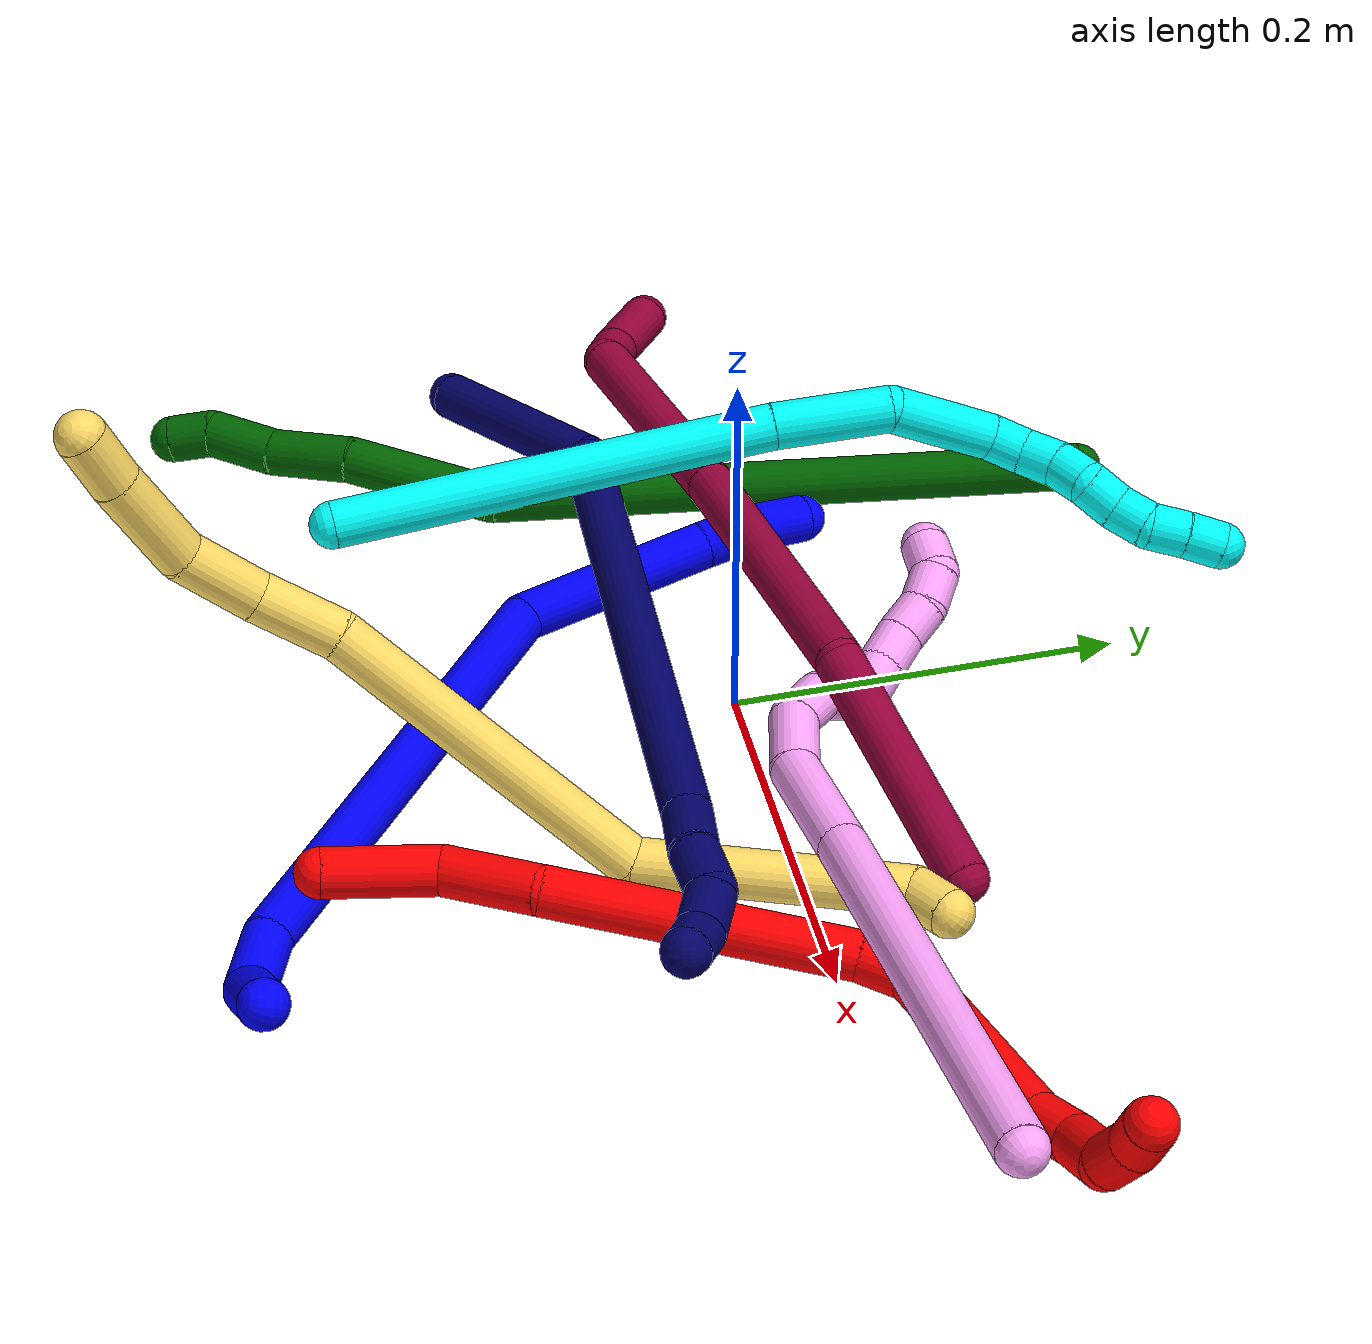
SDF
<sdf version="1.7">
 <world name="default">
  <plugin name="TubeGeneratorPlugin" filename="libtube_generator_plugin.so"/>
  <model name="photoneo_s_sensor">
   <static>1</static>
   <pose>0 0 2 1.57079 1.57079 3.14159</pose>
   <link name="link">
    <inertial><mass>0.1</mass></inertial>
    <sensor name="sensor" type="depth">
     <update_rate>30</update_rate>
     <camera>
      <horizontal_fov>1.22</horizontal_fov>
      <image><width>1920</width><height>1200</height><format>B8G8R8</format></image>
      <clip><near>0.1</near><far>4</far></clip>
      <depth_camera><output>points</output></depth_camera>
     </camera>
     <plugin name="camera_plugin" filename="libgazebo_ros_depth_camera.so">
      <baseline>0.2</baseline>
      <alwaysOn>1</alwaysOn>
      <updateRate>0.0</updateRate>
      <cameraName>camera_ir</cameraName>
      <imageTopicName>/camera/color/image_raw</imageTopicName>
      <cameraInfoTopicName>/camera/color/camera_info</cameraInfoTopicName>
      <depthImageTopicName>/camera/depth/image_raw</depthImageTopicName>
      <depthImageCameraInfoTopicName>/camera/depth/camera_info</depthImageCameraInfoTopicName>
      <pointCloudTopicName>/camera/depth/points</pointCloudTopicName>
      <frameName>fr_optical</frameName>
      <pointCloudCutoff>0.1</pointCloudCutoff>
      <pointCloudCutoffMax>2.0</pointCloudCutoffMax>
      <distortionK1>0</distortionK1>
      <distortionK2>0</distortionK2>
      <distortionK3>0</distortionK3>
      <distortionT1>0</distortionT1>
      <distortionT2>0</distortionT2>
      <CxPrime>0</CxPrime>
      <Cx>0</Cx>
      <Cy>0</Cy>
      <focalLength>0</focalLength>
      <hackBaseline>0</hackBaseline>
     </plugin>
    </sensor>
   </link>
  </model>
  <gravity>0 0 -9.8</gravity>
  <magnetic_field>6e-06 2.3e-05 -4.2e-05</magnetic_field>
  <atmosphere type="adiabatic"/>
  <physics name="default_physics" default="0" type="ode">
   <max_step_size>0.003</max_step_size>
   <real_time_factor>1</real_time_factor>
   <real_time_update_rate>1000</real_time_update_rate>
   <max_contacts>10000</max_contacts>
   <ode>
    <solver>
     <type>quick</type>
     <iters>100</iters>
     <sor>1.3</sor>
     <use_dynamic_moi_rescaling>0</use_dynamic_moi_rescaling>
    </solver>
    <constraints>
     <contact_max_correcting_vel>0</contact_max_correcting_vel>
     <contact_surface_layer>0.001</contact_surface_layer>
     <cfm>0</cfm>
     <erp>0.2</erp>
    </constraints>
   </ode>
  </physics>
  <scene><ambient>0.4 0.4 0.4 1</ambient><background>0.7 0.7 0.7 1</background><shadows>0</shadows></scene>
  <audio><device>default</device></audio>
  <spherical_coordinates>
   <surface_model>EARTH_WGS84</surface_model>
   <latitude_deg>0</latitude_deg>
   <longitude_deg>0</longitude_deg>
   <elevation>0</elevation>
   <heading_deg>0</heading_deg>
  </spherical_coordinates>
  <model name="bin">
   <static>1</static>
   <link name="bottom">
    <collision name="collision-bottom">
     <pose>0 0 -0.01 0 -0 0</pose>
     <geometry><box><size>0.8 0.6 0.02</size></box></geometry>
     <surface>
      <friction><ode><mu>100</mu><mu2>100</mu2></ode></friction>
      <contact><collide_bitmask>65535</collide_bitmask></contact>
     </surface>
    </collision>
   </link>
   <link name="west_wall">
    <collision name="collision-west_wall">
     <pose>-0.41 0 0.1 0 -0 0</pose>
     <geometry><box><size>0.02 0.6 0.2</size></box></geometry>
     <surface>
      <friction><ode><mu>100</mu><mu2>100</mu2></ode></friction>
      <contact><collide_bitmask>65535</collide_bitmask></contact>
     </surface>
    </collision>
   </link>
   <link name="east_wall">
    <collision name="collision-east_wall">
     <pose>0.41 0 0.1 0 -0 0</pose>
     <geometry><box><size>0.02 0.6 0.2</size></box></geometry>
     <surface>
      <friction><ode><mu>100</mu><mu2>100</mu2></ode></friction>
      <contact><collide_bitmask>65535</collide_bitmask></contact>
     </surface>
    </collision>
   </link>
   <link name="south_wall">
    <collision name="collision-south_wall">
     <pose>0 -0.31 0.1 0 -0 0</pose>
     <geometry><box><size>0.8 0.02 0.2</size></box></geometry>
     <surface>
      <friction><ode><mu>100</mu><mu2>100</mu2></ode></friction>
      <contact><collide_bitmask>65535</collide_bitmask></contact>
     </surface>
    </collision>
   </link>
   <link name="north_wall">
    <collision name="collision-north_wall">
     <pose>0 0.31 0.1 0 -0 0</pose>
     <geometry><box><size>0.8 0.02 0.2</size></box></geometry>
     <surface>
      <friction><ode><mu>100</mu><mu2>100</mu2></ode></friction>
      <contact><collide_bitmask>65535</collide_bitmask></contact>
     </surface>
    </collision>
   </link>
  </model>
  <model name="1">
   <static>0</static>
   <link name="1">
    <collision name="collision-cylinder-e_1_1_4">
     <pose>-0.018962 -0.005473 -0.005188 2.32944 -1.19227 -2.01189</pose>
     <geometry><cylinder><radius>0.0125</radius><length>0.040814</length></cylinder></geometry>
     <surface>
      <friction><ode><mu>1.16</mu><mu2>1.16</mu2><slip1>0</slip1><slip2>0</slip2></ode></friction>
      <contact><ode><kp>1e+06</kp><kd>1</kd><max_vel>0</max_vel><min_depth>0.001</min_depth></ode></contact>
     </surface>
    </collision>
    <visual name="visual-cylinder-e_1_1_4">
     <pose>-0.018962 -0.005473 -0.005188 2.32944 -1.19227 -2.01189</pose>
     <geometry><cylinder><radius>0.0125</radius><length>0.040814</length></cylinder></geometry>
     <material><ambient>0 0 1 1</ambient></material>
    </visual>
    <collision name="collision-cylinder-e_2_4_5">
     <pose>-0.052261 -0.00319 -0.017842 -2.33709 -0.926681 1.7308</pose>
     <geometry><cylinder><radius>0.0125</radius><length>0.035857</length></cylinder></geometry>
     <surface>
      <friction><ode><mu>1.16</mu><mu2>1.16</mu2><slip1>0</slip1><slip2>0</slip2></ode></friction>
      <contact><ode><kp>1e+06</kp><kd>1</kd><max_vel>0</max_vel><min_depth>0.001</min_depth></ode></contact>
     </surface>
    </collision>
    <visual name="visual-cylinder-e_2_4_5">
     <pose>-0.052261 -0.00319 -0.017842 -2.33709 -0.926681 1.7308</pose>
     <geometry><cylinder><radius>0.0125</radius><length>0.035857</length></cylinder></geometry>
     <material><ambient>0 0 1 1</ambient></material>
    </visual>
    <collision name="collision-cylinder-e_3_5_6">
     <pose>-0.14315 0.068947 -0.10562 -2.46586 -0.63947 1.51148</pose>
     <geometry><cylinder><radius>0.0125</radius><length>0.256555</length></cylinder></geometry>
     <surface>
      <friction><ode><mu>1.16</mu><mu2>1.16</mu2><slip1>0</slip1><slip2>0</slip2></ode></friction>
      <contact><ode><kp>1e+06</kp><kd>1</kd><max_vel>0</max_vel><min_depth>0.001</min_depth></ode></contact>
     </surface>
    </collision>
    <visual name="visual-cylinder-e_3_5_6">
     <pose>-0.14315 0.068947 -0.10562 -2.46586 -0.63947 1.51148</pose>
     <geometry><cylinder><radius>0.0125</radius><length>0.256555</length></cylinder></geometry>
     <material><ambient>0 0 1 1</ambient></material>
    </visual>
    <collision name="collision-cylinder-e_4_6_7">
     <pose>-0.224131 0.160175 -0.232559 -2.61917 -0.082138 0.305051</pose>
     <geometry><cylinder><radius>0.0125</radius><length>0.107972</length></cylinder></geometry>
     <surface>
      <friction><ode><mu>1.16</mu><mu2>1.16</mu2><slip1>0</slip1><slip2>0</slip2></ode></friction>
      <contact><ode><kp>1e+06</kp><kd>1</kd><max_vel>0</max_vel><min_depth>0.001</min_depth></ode></contact>
     </surface>
    </collision>
    <visual name="visual-cylinder-e_4_6_7">
     <pose>-0.224131 0.160175 -0.232559 -2.61917 -0.082138 0.305051</pose>
     <geometry><cylinder><radius>0.0125</radius><length>0.107972</length></cylinder></geometry>
     <material><ambient>0 0 1 1</ambient></material>
    </visual>
    <collision name="collision-cylinder-e_5_7_8">
     <pose>-0.227278 0.19406 -0.289602 -2.54738 0.101649 -0.32928</pose>
     <geometry><cylinder><radius>0.0125</radius><length>0.025273</length></cylinder></geometry>
     <surface>
      <friction><ode><mu>1.16</mu><mu2>1.16</mu2><slip1>0</slip1><slip2>0</slip2></ode></friction>
      <contact><ode><kp>1e+06</kp><kd>1</kd><max_vel>0</max_vel><min_depth>0.001</min_depth></ode></contact>
     </surface>
    </collision>
    <visual name="visual-cylinder-e_5_7_8">
     <pose>-0.227278 0.19406 -0.289602 -2.54738 0.101649 -0.32928</pose>
     <geometry><cylinder><radius>0.0125</radius><length>0.025273</length></cylinder></geometry>
     <material><ambient>0 0 1 1</ambient></material>
    </visual>
    <collision name="collision-cylinder-e_6_8_2">
     <pose>-0.227291 0.206618 -0.315796 -2.80505 -0.077322 0.44775</pose>
     <geometry><cylinder><radius>0.0125</radius><length>0.033529</length></cylinder></geometry>
     <surface>
      <friction><ode><mu>1.16</mu><mu2>1.16</mu2><slip1>0</slip1><slip2>0</slip2></ode></friction>
      <contact><ode><kp>1e+06</kp><kd>1</kd><max_vel>0</max_vel><min_depth>0.001</min_depth></ode></contact>
     </surface>
    </collision>
    <visual name="visual-cylinder-e_6_8_2">
     <pose>-0.227291 0.206618 -0.315796 -2.80505 -0.077322 0.44775</pose>
     <geometry><cylinder><radius>0.0125</radius><length>0.033529</length></cylinder></geometry>
     <material><ambient>0 0 1 1</ambient></material>
    </visual>
    <collision name="collision-sphere-2">
     <pose>-0.228586 0.212138 -0.331573 0 -0 0</pose>
     <geometry><sphere><radius>0.0125</radius></sphere></geometry>
     <surface>
      <friction><ode><mu>1.16</mu><mu2>1.16</mu2><slip1>0</slip1><slip2>0</slip2></ode></friction>
      <contact><ode><kp>1e+06</kp><kd>1</kd><max_vel>0</max_vel><min_depth>0.001</min_depth></ode></contact>
     </surface>
    </collision>
    <visual name="visual-sphere-2">
     <pose>-0.228586 0.212138 -0.331573 0 -0 0</pose>
     <geometry><sphere><radius>0.0125</radius></sphere></geometry>
     <material><ambient>0 0 1 1</ambient></material>
    </visual>
    <collision name="collision-sphere-4">
     <pose>-0.037925 -0.010947 -0.010376 0 -0 0</pose>
     <geometry><sphere><radius>0.0125</radius></sphere></geometry>
     <surface>
      <friction><ode><mu>1.16</mu><mu2>1.16</mu2><slip1>0</slip1><slip2>0</slip2></ode></friction>
      <contact><ode><kp>1e+06</kp><kd>1</kd><max_vel>0</max_vel><min_depth>0.001</min_depth></ode></contact>
     </surface>
    </collision>
    <visual name="visual-sphere-4">
     <pose>-0.037925 -0.010947 -0.010376 0 -0 0</pose>
     <geometry><sphere><radius>0.0125</radius></sphere></geometry>
     <material><ambient>0 0 1 1</ambient></material>
    </visual>
    <collision name="collision-sphere-1">
     <geometry><sphere><radius>0.0125</radius></sphere></geometry>
     <surface>
      <friction><ode><mu>1.16</mu><mu2>1.16</mu2><slip1>0</slip1><slip2>0</slip2></ode></friction>
      <contact><ode><kp>1e+06</kp><kd>1</kd><max_vel>0</max_vel><min_depth>0.001</min_depth></ode></contact>
     </surface>
    </collision>
    <visual name="visual-sphere-1">
     <geometry><sphere><radius>0.0125</radius></sphere></geometry>
     <material><ambient>0 0 1 1</ambient></material>
    </visual>
    <collision name="collision-sphere-8">
     <pose>-0.225996 0.201098 -0.300019 0 -0 0</pose>
     <geometry><sphere><radius>0.0125</radius></sphere></geometry>
     <surface>
      <friction><ode><mu>1.16</mu><mu2>1.16</mu2><slip1>0</slip1><slip2>0</slip2></ode></friction>
      <contact><ode><kp>1e+06</kp><kd>1</kd><max_vel>0</max_vel><min_depth>0.001</min_depth></ode></contact>
     </surface>
    </collision>
    <visual name="visual-sphere-8">
     <pose>-0.225996 0.201098 -0.300019 0 -0 0</pose>
     <geometry><sphere><radius>0.0125</radius></sphere></geometry>
     <material><ambient>0 0 1 1</ambient></material>
    </visual>
    <collision name="collision-sphere-5">
     <pose>-0.066597 0.004567 -0.025308 0 -0 0</pose>
     <geometry><sphere><radius>0.0125</radius></sphere></geometry>
     <surface>
      <friction><ode><mu>1.16</mu><mu2>1.16</mu2><slip1>0</slip1><slip2>0</slip2></ode></friction>
      <contact><ode><kp>1e+06</kp><kd>1</kd><max_vel>0</max_vel><min_depth>0.001</min_depth></ode></contact>
     </surface>
    </collision>
    <visual name="visual-sphere-5">
     <pose>-0.066597 0.004567 -0.025308 0 -0 0</pose>
     <geometry><sphere><radius>0.0125</radius></sphere></geometry>
     <material><ambient>0 0 1 1</ambient></material>
    </visual>
    <collision name="collision-sphere-6">
     <pose>-0.219702 0.133328 -0.185932 0 -0 0</pose>
     <geometry><sphere><radius>0.0125</radius></sphere></geometry>
     <surface>
      <friction><ode><mu>1.16</mu><mu2>1.16</mu2><slip1>0</slip1><slip2>0</slip2></ode></friction>
      <contact><ode><kp>1e+06</kp><kd>1</kd><max_vel>0</max_vel><min_depth>0.001</min_depth></ode></contact>
     </surface>
    </collision>
    <visual name="visual-sphere-6">
     <pose>-0.219702 0.133328 -0.185932 0 -0 0</pose>
     <geometry><sphere><radius>0.0125</radius></sphere></geometry>
     <material><ambient>0 0 1 1</ambient></material>
    </visual>
    <collision name="collision-sphere-7">
     <pose>-0.22856 0.187022 -0.279186 0 -0 0</pose>
     <geometry><sphere><radius>0.0125</radius></sphere></geometry>
     <surface>
      <friction><ode><mu>1.16</mu><mu2>1.16</mu2><slip1>0</slip1><slip2>0</slip2></ode></friction>
      <contact><ode><kp>1e+06</kp><kd>1</kd><max_vel>0</max_vel><min_depth>0.001</min_depth></ode></contact>
     </surface>
    </collision>
    <visual name="visual-sphere-7">
     <pose>-0.22856 0.187022 -0.279186 0 -0 0</pose>
     <geometry><sphere><radius>0.0125</radius></sphere></geometry>
     <material><ambient>0 0 1 1</ambient></material>
    </visual>
    <inertial>
     <pose>-0.153876 0.092955 -0.141932 0 -0 0</pose>
     <mass>0.5</mass>
     <inertia>
      <ixx>0.001328</ixx>
      <ixy>0</ixy>
      <ixz>0</ixz>
      <iyy>0.001565</iyy>
      <iyz>0</iyz>
      <izz>7.1e-05</izz>
     </inertia>
    </inertial>
   </link>
   <pose>0.187484 -0.265949 0.037028 1.08892 -0.259809 0.220103</pose>
  </model>
  <model name="2">
   <static>0</static>
   <link name="2">
    <collision name="collision-cylinder-e_1_1_4">
     <pose>0.02378 0.016461 -0.001014 -1.63232 0.964416 -1.01588</pose>
     <geometry><cylinder><radius>0.0125</radius><length>0.057879</length></cylinder></geometry>
     <surface>
      <friction><ode><mu>1.16</mu><mu2>1.16</mu2><slip1>0</slip1><slip2>0</slip2></ode></friction>
      <contact><ode><kp>1e+06</kp><kd>1</kd><max_vel>0</max_vel><min_depth>0.001</min_depth></ode></contact>
     </surface>
    </collision>
    <visual name="visual-cylinder-e_1_1_4">
     <pose>0.02378 0.016461 -0.001014 -1.63232 0.964416 -1.01588</pose>
     <geometry><cylinder><radius>0.0125</radius><length>0.057879</length></cylinder></geometry>
     <material><ambient>1 0 0 1</ambient></material>
    </visual>
    <collision name="collision-cylinder-e_2_4_5">
     <pose>0.05946 0.054369 -0.009586 -1.9096 0.482105 -0.668497</pose>
     <geometry><cylinder><radius>0.0125</radius><length>0.051329</length></cylinder></geometry>
     <surface>
      <friction><ode><mu>1.16</mu><mu2>1.16</mu2><slip1>0</slip1><slip2>0</slip2></ode></friction>
      <contact><ode><kp>1e+06</kp><kd>1</kd><max_vel>0</max_vel><min_depth>0.001</min_depth></ode></contact>
     </surface>
    </collision>
    <visual name="visual-cylinder-e_2_4_5">
     <pose>0.05946 0.054369 -0.009586 -1.9096 0.482105 -0.668497</pose>
     <geometry><cylinder><radius>0.0125</radius><length>0.051329</length></cylinder></geometry>
     <material><ambient>1 0 0 1</ambient></material>
    </visual>
    <collision name="collision-cylinder-e_3_5_6">
     <pose>0.11991 0.134198 -0.019774 -1.61583 0.693225 -0.722515</pose>
     <geometry><cylinder><radius>0.0125</radius><length>0.151956</length></cylinder></geometry>
     <surface>
      <friction><ode><mu>1.16</mu><mu2>1.16</mu2><slip1>0</slip1><slip2>0</slip2></ode></friction>
      <contact><ode><kp>1e+06</kp><kd>1</kd><max_vel>0</max_vel><min_depth>0.001</min_depth></ode></contact>
     </surface>
    </collision>
    <visual name="visual-cylinder-e_3_5_6">
     <pose>0.11991 0.134198 -0.019774 -1.61583 0.693225 -0.722515</pose>
     <geometry><cylinder><radius>0.0125</radius><length>0.151956</length></cylinder></geometry>
     <material><ambient>1 0 0 1</ambient></material>
    </visual>
    <collision name="collision-cylinder-e_4_6_7">
     <pose>0.174373 0.203882 -0.023126 -1.63443 0.481049 -0.511356</pose>
     <geometry><cylinder><radius>0.0125</radius><length>0.025549</length></cylinder></geometry>
     <surface>
      <friction><ode><mu>1.16</mu><mu2>1.16</mu2><slip1>0</slip1><slip2>0</slip2></ode></friction>
      <contact><ode><kp>1e+06</kp><kd>1</kd><max_vel>0</max_vel><min_depth>0.001</min_depth></ode></contact>
     </surface>
    </collision>
    <visual name="visual-cylinder-e_4_6_7">
     <pose>0.174373 0.203882 -0.023126 -1.63443 0.481049 -0.511356</pose>
     <geometry><cylinder><radius>0.0125</radius><length>0.025549</length></cylinder></geometry>
     <material><ambient>1 0 0 1</ambient></material>
    </visual>
    <collision name="collision-cylinder-e_5_7_8">
     <pose>0.167364 0.266506 -0.043461 -1.93587 -0.230951 0.333879</pose>
     <geometry><cylinder><radius>0.0125</radius><length>0.112883</length></cylinder></geometry>
     <surface>
      <friction><ode><mu>1.16</mu><mu2>1.16</mu2><slip1>0</slip1><slip2>0</slip2></ode></friction>
      <contact><ode><kp>1e+06</kp><kd>1</kd><max_vel>0</max_vel><min_depth>0.001</min_depth></ode></contact>
     </surface>
    </collision>
    <visual name="visual-cylinder-e_5_7_8">
     <pose>0.167364 0.266506 -0.043461 -1.93587 -0.230951 0.333879</pose>
     <geometry><cylinder><radius>0.0125</radius><length>0.112883</length></cylinder></geometry>
     <material><ambient>1 0 0 1</ambient></material>
    </visual>
    <collision name="collision-cylinder-e_6_8_9">
     <pose>0.154065 0.329092 -0.069154 -2.06549 -0.029623 0.049631</pose>
     <geometry><cylinder><radius>0.0125</radius><length>0.02561</length></cylinder></geometry>
     <surface>
      <friction><ode><mu>1.16</mu><mu2>1.16</mu2><slip1>0</slip1><slip2>0</slip2></ode></friction>
      <contact><ode><kp>1e+06</kp><kd>1</kd><max_vel>0</max_vel><min_depth>0.001</min_depth></ode></contact>
     </surface>
    </collision>
    <visual name="visual-cylinder-e_6_8_9">
     <pose>0.154065 0.329092 -0.069154 -2.06549 -0.029623 0.049631</pose>
     <geometry><cylinder><radius>0.0125</radius><length>0.02561</length></cylinder></geometry>
     <material><ambient>1 0 0 1</ambient></material>
    </visual>
    <collision name="collision-cylinder-e_7_9_10">
     <pose>0.148737 0.351502 -0.086062 -2.34196 -0.30825 0.704606</pose>
     <geometry><cylinder><radius>0.0125</radius><length>0.03262</length></cylinder></geometry>
     <surface>
      <friction><ode><mu>1.16</mu><mu2>1.16</mu2><slip1>0</slip1><slip2>0</slip2></ode></friction>
      <contact><ode><kp>1e+06</kp><kd>1</kd><max_vel>0</max_vel><min_depth>0.001</min_depth></ode></contact>
     </surface>
    </collision>
    <visual name="visual-cylinder-e_7_9_10">
     <pose>0.148737 0.351502 -0.086062 -2.34196 -0.30825 0.704606</pose>
     <geometry><cylinder><radius>0.0125</radius><length>0.03262</length></cylinder></geometry>
     <material><ambient>1 0 0 1</ambient></material>
    </visual>
    <collision name="collision-cylinder-e_8_10_11">
     <pose>0.146324 0.366188 -0.10703 -2.80541 0.231797 -1.20263</pose>
     <geometry><cylinder><radius>0.0125</radius><length>0.022065</length></cylinder></geometry>
     <surface>
      <friction><ode><mu>1.16</mu><mu2>1.16</mu2><slip1>0</slip1><slip2>0</slip2></ode></friction>
      <contact><ode><kp>1e+06</kp><kd>1</kd><max_vel>0</max_vel><min_depth>0.001</min_depth></ode></contact>
     </surface>
    </collision>
    <visual name="visual-cylinder-e_8_10_11">
     <pose>0.146324 0.366188 -0.10703 -2.80541 0.231797 -1.20263</pose>
     <geometry><cylinder><radius>0.0125</radius><length>0.022065</length></cylinder></geometry>
     <material><ambient>1 0 0 1</ambient></material>
    </visual>
    <collision name="collision-cylinder-e_9_11_2">
     <pose>0.1492 0.370983 -0.127137 -3.01666 0.034002 -0.530834</pose>
     <geometry><cylinder><radius>0.0125</radius><length>0.02011</length></cylinder></geometry>
     <surface>
      <friction><ode><mu>1.16</mu><mu2>1.16</mu2><slip1>0</slip1><slip2>0</slip2></ode></friction>
      <contact><ode><kp>1e+06</kp><kd>1</kd><max_vel>0</max_vel><min_depth>0.001</min_depth></ode></contact>
     </surface>
    </collision>
    <visual name="visual-cylinder-e_9_11_2">
     <pose>0.1492 0.370983 -0.127137 -3.01666 0.034002 -0.530834</pose>
     <geometry><cylinder><radius>0.0125</radius><length>0.02011</length></cylinder></geometry>
     <material><ambient>1 0 0 1</ambient></material>
    </visual>
    <collision name="collision-sphere-2">
     <pose>0.149542 0.372235 -0.137108 0 -0 0</pose>
     <geometry><sphere><radius>0.0125</radius></sphere></geometry>
     <surface>
      <friction><ode><mu>1.16</mu><mu2>1.16</mu2><slip1>0</slip1><slip2>0</slip2></ode></friction>
      <contact><ode><kp>1e+06</kp><kd>1</kd><max_vel>0</max_vel><min_depth>0.001</min_depth></ode></contact>
     </surface>
    </collision>
    <visual name="visual-sphere-2">
     <pose>0.149542 0.372235 -0.137108 0 -0 0</pose>
     <geometry><sphere><radius>0.0125</radius></sphere></geometry>
     <material><ambient>1 0 0 1</ambient></material>
    </visual>
    <collision name="collision-sphere-11">
     <pose>0.148858 0.369731 -0.117167 0 -0 0</pose>
     <geometry><sphere><radius>0.0125</radius></sphere></geometry>
     <surface>
      <friction><ode><mu>1.16</mu><mu2>1.16</mu2><slip1>0</slip1><slip2>0</slip2></ode></friction>
      <contact><ode><kp>1e+06</kp><kd>1</kd><max_vel>0</max_vel><min_depth>0.001</min_depth></ode></contact>
     </surface>
    </collision>
    <visual name="visual-sphere-11">
     <pose>0.148858 0.369731 -0.117167 0 -0 0</pose>
     <geometry><sphere><radius>0.0125</radius></sphere></geometry>
     <material><ambient>1 0 0 1</ambient></material>
    </visual>
    <collision name="collision-sphere-10">
     <pose>0.143789 0.362646 -0.096894 0 -0 0</pose>
     <geometry><sphere><radius>0.0125</radius></sphere></geometry>
     <surface>
      <friction><ode><mu>1.16</mu><mu2>1.16</mu2><slip1>0</slip1><slip2>0</slip2></ode></friction>
      <contact><ode><kp>1e+06</kp><kd>1</kd><max_vel>0</max_vel><min_depth>0.001</min_depth></ode></contact>
     </surface>
    </collision>
    <visual name="visual-sphere-10">
     <pose>0.143789 0.362646 -0.096894 0 -0 0</pose>
     <geometry><sphere><radius>0.0125</radius></sphere></geometry>
     <material><ambient>1 0 0 1</ambient></material>
    </visual>
    <collision name="collision-sphere-9">
     <pose>0.153686 0.340357 -0.07523 0 -0 0</pose>
     <geometry><sphere><radius>0.0125</radius></sphere></geometry>
     <surface>
      <friction><ode><mu>1.16</mu><mu2>1.16</mu2><slip1>0</slip1><slip2>0</slip2></ode></friction>
      <contact><ode><kp>1e+06</kp><kd>1</kd><max_vel>0</max_vel><min_depth>0.001</min_depth></ode></contact>
     </surface>
    </collision>
    <visual name="visual-sphere-9">
     <pose>0.153686 0.340357 -0.07523 0 -0 0</pose>
     <geometry><sphere><radius>0.0125</radius></sphere></geometry>
     <material><ambient>1 0 0 1</ambient></material>
    </visual>
    <collision name="collision-sphere-4">
     <pose>0.04756 0.032923 -0.002028 0 -0 0</pose>
     <geometry><sphere><radius>0.0125</radius></sphere></geometry>
     <surface>
      <friction><ode><mu>1.16</mu><mu2>1.16</mu2><slip1>0</slip1><slip2>0</slip2></ode></friction>
      <contact><ode><kp>1e+06</kp><kd>1</kd><max_vel>0</max_vel><min_depth>0.001</min_depth></ode></contact>
     </surface>
    </collision>
    <visual name="visual-sphere-4">
     <pose>0.04756 0.032923 -0.002028 0 -0 0</pose>
     <geometry><sphere><radius>0.0125</radius></sphere></geometry>
     <material><ambient>1 0 0 1</ambient></material>
    </visual>
    <collision name="collision-sphere-1">
     <geometry><sphere><radius>0.0125</radius></sphere></geometry>
     <surface>
      <friction><ode><mu>1.16</mu><mu2>1.16</mu2><slip1>0</slip1><slip2>0</slip2></ode></friction>
      <contact><ode><kp>1e+06</kp><kd>1</kd><max_vel>0</max_vel><min_depth>0.001</min_depth></ode></contact>
     </surface>
    </collision>
    <visual name="visual-sphere-1">
     <geometry><sphere><radius>0.0125</radius></sphere></geometry>
     <material><ambient>1 0 0 1</ambient></material>
    </visual>
    <collision name="collision-sphere-8">
     <pose>0.154444 0.317827 -0.063077 0 -0 0</pose>
     <geometry><sphere><radius>0.0125</radius></sphere></geometry>
     <surface>
      <friction><ode><mu>1.16</mu><mu2>1.16</mu2><slip1>0</slip1><slip2>0</slip2></ode></friction>
      <contact><ode><kp>1e+06</kp><kd>1</kd><max_vel>0</max_vel><min_depth>0.001</min_depth></ode></contact>
     </surface>
    </collision>
    <visual name="visual-sphere-8">
     <pose>0.154444 0.317827 -0.063077 0 -0 0</pose>
     <geometry><sphere><radius>0.0125</radius></sphere></geometry>
     <material><ambient>1 0 0 1</ambient></material>
    </visual>
    <collision name="collision-sphere-5">
     <pose>0.071359 0.075816 -0.017143 0 -0 0</pose>
     <geometry><sphere><radius>0.0125</radius></sphere></geometry>
     <surface>
      <friction><ode><mu>1.16</mu><mu2>1.16</mu2><slip1>0</slip1><slip2>0</slip2></ode></friction>
      <contact><ode><kp>1e+06</kp><kd>1</kd><max_vel>0</max_vel><min_depth>0.001</min_depth></ode></contact>
     </surface>
    </collision>
    <visual name="visual-sphere-5">
     <pose>0.071359 0.075816 -0.017143 0 -0 0</pose>
     <geometry><sphere><radius>0.0125</radius></sphere></geometry>
     <material><ambient>1 0 0 1</ambient></material>
    </visual>
    <collision name="collision-sphere-6">
     <pose>0.168462 0.19258 -0.022405 0 -0 0</pose>
     <geometry><sphere><radius>0.0125</radius></sphere></geometry>
     <surface>
      <friction><ode><mu>1.16</mu><mu2>1.16</mu2><slip1>0</slip1><slip2>0</slip2></ode></friction>
      <contact><ode><kp>1e+06</kp><kd>1</kd><max_vel>0</max_vel><min_depth>0.001</min_depth></ode></contact>
     </surface>
    </collision>
    <visual name="visual-sphere-6">
     <pose>0.168462 0.19258 -0.022405 0 -0 0</pose>
     <geometry><sphere><radius>0.0125</radius></sphere></geometry>
     <material><ambient>1 0 0 1</ambient></material>
    </visual>
    <collision name="collision-sphere-7">
     <pose>0.180284 0.215184 -0.023846 0 -0 0</pose>
     <geometry><sphere><radius>0.0125</radius></sphere></geometry>
     <surface>
      <friction><ode><mu>1.16</mu><mu2>1.16</mu2><slip1>0</slip1><slip2>0</slip2></ode></friction>
      <contact><ode><kp>1e+06</kp><kd>1</kd><max_vel>0</max_vel><min_depth>0.001</min_depth></ode></contact>
     </surface>
    </collision>
    <visual name="visual-sphere-7">
     <pose>0.180284 0.215184 -0.023846 0 -0 0</pose>
     <geometry><sphere><radius>0.0125</radius></sphere></geometry>
     <material><ambient>1 0 0 1</ambient></material>
    </visual>
    <inertial>
     <pose>0.122047 0.189725 -0.037098 0 -0 0</pose>
     <mass>0.5</mass>
     <inertia>
      <ixx>0.000193</ixx>
      <ixy>0</ixy>
      <ixz>0</ixz>
      <iyy>-9e-06</iyy>
      <iyz>0</iyz>
      <izz>-0.000566</izz>
     </inertia>
    </inertial>
   </link>
   <pose>0.105668 -0.227418 0.033177 -2.90918 -0.025899 2.04442</pose>
  </model>
  <model name="3">
   <static>0</static>
   <link name="3">
    <collision name="collision-cylinder-e_1_1_4">
     <pose>0.007689 0.003064 0.116987 -0.026188 0.065609 -0.000859</pose>
     <geometry><cylinder><radius>0.0125</radius><length>0.23456</length></cylinder></geometry>
     <surface>
      <friction><ode><mu>1.16</mu><mu2>1.16</mu2><slip1>0</slip1><slip2>0</slip2></ode></friction>
      <contact><ode><kp>1e+06</kp><kd>1</kd><max_vel>0</max_vel><min_depth>0.001</min_depth></ode></contact>
     </surface>
    </collision>
    <visual name="visual-cylinder-e_1_1_4">
     <pose>0.007689 0.003064 0.116987 -0.026188 0.065609 -0.000859</pose>
     <geometry><cylinder><radius>0.0125</radius><length>0.23456</length></cylinder></geometry>
     <material><ambient>0.003922 1 0.996078 1</ambient></material>
    </visual>
    <collision name="collision-cylinder-e_2_4_5">
     <pose>0.018826 0.004535 0.265219 0.050969 0.109756 0.002801</pose>
     <geometry><cylinder><radius>0.0125</radius><length>0.062949</length></cylinder></geometry>
     <surface>
      <friction><ode><mu>1.16</mu><mu2>1.16</mu2><slip1>0</slip1><slip2>0</slip2></ode></friction>
      <contact><ode><kp>1e+06</kp><kd>1</kd><max_vel>0</max_vel><min_depth>0.001</min_depth></ode></contact>
     </surface>
    </collision>
    <visual name="visual-cylinder-e_2_4_5">
     <pose>0.018826 0.004535 0.265219 0.050969 0.109756 0.002801</pose>
     <geometry><cylinder><radius>0.0125</radius><length>0.062949</length></cylinder></geometry>
     <material><ambient>0.003922 1 0.996078 1</ambient></material>
    </visual>
    <collision name="collision-cylinder-e_3_5_6">
     <pose>0.039703 0.007944 0.321644 -0.196141 0.596427 -0.060465</pose>
     <geometry><cylinder><radius>0.0125</radius><length>0.06206</length></cylinder></geometry>
     <surface>
      <friction><ode><mu>1.16</mu><mu2>1.16</mu2><slip1>0</slip1><slip2>0</slip2></ode></friction>
      <contact><ode><kp>1e+06</kp><kd>1</kd><max_vel>0</max_vel><min_depth>0.001</min_depth></ode></contact>
     </surface>
    </collision>
    <visual name="visual-cylinder-e_3_5_6">
     <pose>0.039703 0.007944 0.321644 -0.196141 0.596427 -0.060465</pose>
     <geometry><cylinder><radius>0.0125</radius><length>0.06206</length></cylinder></geometry>
     <material><ambient>0.003922 1 0.996078 1</ambient></material>
    </visual>
    <collision name="collision-cylinder-e_4_6_7">
     <pose>0.062358 0.009008 0.354539 0.472218 0.542884 0.133722</pose>
     <geometry><cylinder><radius>0.0125</radius><length>0.020232</length></cylinder></geometry>
     <surface>
      <friction><ode><mu>1.16</mu><mu2>1.16</mu2><slip1>0</slip1><slip2>0</slip2></ode></friction>
      <contact><ode><kp>1e+06</kp><kd>1</kd><max_vel>0</max_vel><min_depth>0.001</min_depth></ode></contact>
     </surface>
    </collision>
    <visual name="visual-cylinder-e_4_6_7">
     <pose>0.062358 0.009008 0.354539 0.472218 0.542884 0.133722</pose>
     <geometry><cylinder><radius>0.0125</radius><length>0.020232</length></cylinder></geometry>
     <material><ambient>0.003922 1 0.996078 1</ambient></material>
    </visual>
    <collision name="collision-cylinder-e_5_7_8">
     <pose>0.071213 -0.00086 0.36951 0.68485 0.369473 0.133028</pose>
     <geometry><cylinder><radius>0.0125</radius><length>0.020097</length></cylinder></geometry>
     <surface>
      <friction><ode><mu>1.16</mu><mu2>1.16</mu2><slip1>0</slip1><slip2>0</slip2></ode></friction>
      <contact><ode><kp>1e+06</kp><kd>1</kd><max_vel>0</max_vel><min_depth>0.001</min_depth></ode></contact>
     </surface>
    </collision>
    <visual name="visual-cylinder-e_5_7_8">
     <pose>0.071213 -0.00086 0.36951 0.68485 0.369473 0.133028</pose>
     <geometry><cylinder><radius>0.0125</radius><length>0.020097</length></cylinder></geometry>
     <material><ambient>0.003922 1 0.996078 1</ambient></material>
    </visual>
    <collision name="collision-cylinder-e_6_8_9">
     <pose>0.078623 -0.014746 0.381569 1.02799 0.386337 0.219993</pose>
     <geometry><cylinder><radius>0.0125</radius><length>0.020069</length></cylinder></geometry>
     <surface>
      <friction><ode><mu>1.16</mu><mu2>1.16</mu2><slip1>0</slip1><slip2>0</slip2></ode></friction>
      <contact><ode><kp>1e+06</kp><kd>1</kd><max_vel>0</max_vel><min_depth>0.001</min_depth></ode></contact>
     </surface>
    </collision>
    <visual name="visual-cylinder-e_6_8_9">
     <pose>0.078623 -0.014746 0.381569 1.02799 0.386337 0.219993</pose>
     <geometry><cylinder><radius>0.0125</radius><length>0.020069</length></cylinder></geometry>
     <material><ambient>0.003922 1 0.996078 1</ambient></material>
    </visual>
    <collision name="collision-cylinder-e_7_9_10">
     <pose>0.089749 -0.026216 0.392184 0.543242 0.824526 0.242399</pose>
     <geometry><cylinder><radius>0.0125</radius><length>0.020009</length></cylinder></geometry>
     <surface>
      <friction><ode><mu>1.16</mu><mu2>1.16</mu2><slip1>0</slip1><slip2>0</slip2></ode></friction>
      <contact><ode><kp>1e+06</kp><kd>1</kd><max_vel>0</max_vel><min_depth>0.001</min_depth></ode></contact>
     </surface>
    </collision>
    <visual name="visual-cylinder-e_7_9_10">
     <pose>0.089749 -0.026216 0.392184 0.543242 0.824526 0.242399</pose>
     <geometry><cylinder><radius>0.0125</radius><length>0.020009</length></cylinder></geometry>
     <material><ambient>0.003922 1 0.996078 1</ambient></material>
    </visual>
    <collision name="collision-cylinder-e_8_10_11">
     <pose>0.102018 -0.035729 0.404306 0.760598 0.514621 0.209617</pose>
     <geometry><cylinder><radius>0.0125</radius><length>0.020006</length></cylinder></geometry>
     <surface>
      <friction><ode><mu>1.16</mu><mu2>1.16</mu2><slip1>0</slip1><slip2>0</slip2></ode></friction>
      <contact><ode><kp>1e+06</kp><kd>1</kd><max_vel>0</max_vel><min_depth>0.001</min_depth></ode></contact>
     </surface>
    </collision>
    <visual name="visual-cylinder-e_8_10_11">
     <pose>0.102018 -0.035729 0.404306 0.760598 0.514621 0.209617</pose>
     <geometry><cylinder><radius>0.0125</radius><length>0.020006</length></cylinder></geometry>
     <material><ambient>0.003922 1 0.996078 1</ambient></material>
    </visual>
    <collision name="collision-cylinder-e_9_11_12">
     <pose>0.11129 -0.043855 0.419365 0.238126 0.449863 0.054729</pose>
     <geometry><cylinder><radius>0.0125</radius><length>0.02</length></cylinder></geometry>
     <surface>
      <friction><ode><mu>1.16</mu><mu2>1.16</mu2><slip1>0</slip1><slip2>0</slip2></ode></friction>
      <contact><ode><kp>1e+06</kp><kd>1</kd><max_vel>0</max_vel><min_depth>0.001</min_depth></ode></contact>
     </surface>
    </collision>
    <visual name="visual-cylinder-e_9_11_12">
     <pose>0.11129 -0.043855 0.419365 0.238126 0.449863 0.054729</pose>
     <geometry><cylinder><radius>0.0125</radius><length>0.02</length></cylinder></geometry>
     <material><ambient>0.003922 1 0.996078 1</ambient></material>
    </visual>
    <collision name="collision-cylinder-e_10_12_2">
     <pose>0.120573 -0.047992 0.436588 0.233205 0.515547 0.061742</pose>
     <geometry><cylinder><radius>0.0125</radius><length>0.020018</length></cylinder></geometry>
     <surface>
      <friction><ode><mu>1.16</mu><mu2>1.16</mu2><slip1>0</slip1><slip2>0</slip2></ode></friction>
      <contact><ode><kp>1e+06</kp><kd>1</kd><max_vel>0</max_vel><min_depth>0.001</min_depth></ode></contact>
     </surface>
    </collision>
    <visual name="visual-cylinder-e_10_12_2">
     <pose>0.120573 -0.047992 0.436588 0.233205 0.515547 0.061742</pose>
     <geometry><cylinder><radius>0.0125</radius><length>0.020018</length></cylinder></geometry>
     <material><ambient>0.003922 1 0.996078 1</ambient></material>
    </visual>
    <collision name="collision-sphere-2">
     <pose>0.125507 -0.050004 0.445061 0 -0 0</pose>
     <geometry><sphere><radius>0.0125</radius></sphere></geometry>
     <surface>
      <friction><ode><mu>1.16</mu><mu2>1.16</mu2><slip1>0</slip1><slip2>0</slip2></ode></friction>
      <contact><ode><kp>1e+06</kp><kd>1</kd><max_vel>0</max_vel><min_depth>0.001</min_depth></ode></contact>
     </surface>
    </collision>
    <visual name="visual-sphere-2">
     <pose>0.125507 -0.050004 0.445061 0 -0 0</pose>
     <geometry><sphere><radius>0.0125</radius></sphere></geometry>
     <material><ambient>0.003922 1 0.996078 1</ambient></material>
    </visual>
    <collision name="collision-sphere-12">
     <pose>0.115638 -0.04598 0.428116 0 -0 0</pose>
     <geometry><sphere><radius>0.0125</radius></sphere></geometry>
     <surface>
      <friction><ode><mu>1.16</mu><mu2>1.16</mu2><slip1>0</slip1><slip2>0</slip2></ode></friction>
      <contact><ode><kp>1e+06</kp><kd>1</kd><max_vel>0</max_vel><min_depth>0.001</min_depth></ode></contact>
     </surface>
    </collision>
    <visual name="visual-sphere-12">
     <pose>0.115638 -0.04598 0.428116 0 -0 0</pose>
     <geometry><sphere><radius>0.0125</radius></sphere></geometry>
     <material><ambient>0.003922 1 0.996078 1</ambient></material>
    </visual>
    <collision name="collision-sphere-11">
     <pose>0.106941 -0.041731 0.410614 0 -0 0</pose>
     <geometry><sphere><radius>0.0125</radius></sphere></geometry>
     <surface>
      <friction><ode><mu>1.16</mu><mu2>1.16</mu2><slip1>0</slip1><slip2>0</slip2></ode></friction>
      <contact><ode><kp>1e+06</kp><kd>1</kd><max_vel>0</max_vel><min_depth>0.001</min_depth></ode></contact>
     </surface>
    </collision>
    <visual name="visual-sphere-11">
     <pose>0.106941 -0.041731 0.410614 0 -0 0</pose>
     <geometry><sphere><radius>0.0125</radius></sphere></geometry>
     <material><ambient>0.003922 1 0.996078 1</ambient></material>
    </visual>
    <collision name="collision-sphere-10">
     <pose>0.097094 -0.029726 0.397998 0 -0 0</pose>
     <geometry><sphere><radius>0.0125</radius></sphere></geometry>
     <surface>
      <friction><ode><mu>1.16</mu><mu2>1.16</mu2><slip1>0</slip1><slip2>0</slip2></ode></friction>
      <contact><ode><kp>1e+06</kp><kd>1</kd><max_vel>0</max_vel><min_depth>0.001</min_depth></ode></contact>
     </surface>
    </collision>
    <visual name="visual-sphere-10">
     <pose>0.097094 -0.029726 0.397998 0 -0 0</pose>
     <geometry><sphere><radius>0.0125</radius></sphere></geometry>
     <material><ambient>0.003922 1 0.996078 1</ambient></material>
    </visual>
    <collision name="collision-sphere-9">
     <pose>0.082404 -0.022705 0.38637 0 -0 0</pose>
     <geometry><sphere><radius>0.0125</radius></sphere></geometry>
     <surface>
      <friction><ode><mu>1.16</mu><mu2>1.16</mu2><slip1>0</slip1><slip2>0</slip2></ode></friction>
      <contact><ode><kp>1e+06</kp><kd>1</kd><max_vel>0</max_vel><min_depth>0.001</min_depth></ode></contact>
     </surface>
    </collision>
    <visual name="visual-sphere-9">
     <pose>0.082404 -0.022705 0.38637 0 -0 0</pose>
     <geometry><sphere><radius>0.0125</radius></sphere></geometry>
     <material><ambient>0.003922 1 0.996078 1</ambient></material>
    </visual>
    <collision name="collision-sphere-4">
     <pose>0.015378 0.006129 0.233975 0 -0 0</pose>
     <geometry><sphere><radius>0.0125</radius></sphere></geometry>
     <surface>
      <friction><ode><mu>1.16</mu><mu2>1.16</mu2><slip1>0</slip1><slip2>0</slip2></ode></friction>
      <contact><ode><kp>1e+06</kp><kd>1</kd><max_vel>0</max_vel><min_depth>0.001</min_depth></ode></contact>
     </surface>
    </collision>
    <visual name="visual-sphere-4">
     <pose>0.015378 0.006129 0.233975 0 -0 0</pose>
     <geometry><sphere><radius>0.0125</radius></sphere></geometry>
     <material><ambient>0.003922 1 0.996078 1</ambient></material>
    </visual>
    <collision name="collision-sphere-1">
     <geometry><sphere><radius>0.0125</radius></sphere></geometry>
     <surface>
      <friction><ode><mu>1.16</mu><mu2>1.16</mu2><slip1>0</slip1><slip2>0</slip2></ode></friction>
      <contact><ode><kp>1e+06</kp><kd>1</kd><max_vel>0</max_vel><min_depth>0.001</min_depth></ode></contact>
     </surface>
    </collision>
    <visual name="visual-sphere-1">
     <geometry><sphere><radius>0.0125</radius></sphere></geometry>
     <material><ambient>0.003922 1 0.996078 1</ambient></material>
    </visual>
    <collision name="collision-sphere-8">
     <pose>0.074842 -0.006787 0.376768 0 -0 0</pose>
     <geometry><sphere><radius>0.0125</radius></sphere></geometry>
     <surface>
      <friction><ode><mu>1.16</mu><mu2>1.16</mu2><slip1>0</slip1><slip2>0</slip2></ode></friction>
      <contact><ode><kp>1e+06</kp><kd>1</kd><max_vel>0</max_vel><min_depth>0.001</min_depth></ode></contact>
     </surface>
    </collision>
    <visual name="visual-sphere-8">
     <pose>0.074842 -0.006787 0.376768 0 -0 0</pose>
     <geometry><sphere><radius>0.0125</radius></sphere></geometry>
     <material><ambient>0.003922 1 0.996078 1</ambient></material>
    </visual>
    <collision name="collision-sphere-5">
     <pose>0.022273 0.002941 0.296464 0 -0 0</pose>
     <geometry><sphere><radius>0.0125</radius></sphere></geometry>
     <surface>
      <friction><ode><mu>1.16</mu><mu2>1.16</mu2><slip1>0</slip1><slip2>0</slip2></ode></friction>
      <contact><ode><kp>1e+06</kp><kd>1</kd><max_vel>0</max_vel><min_depth>0.001</min_depth></ode></contact>
     </surface>
    </collision>
    <visual name="visual-sphere-5">
     <pose>0.022273 0.002941 0.296464 0 -0 0</pose>
     <geometry><sphere><radius>0.0125</radius></sphere></geometry>
     <material><ambient>0.003922 1 0.996078 1</ambient></material>
    </visual>
    <collision name="collision-sphere-6">
     <pose>0.057132 0.012947 0.346825 0 -0 0</pose>
     <geometry><sphere><radius>0.0125</radius></sphere></geometry>
     <surface>
      <friction><ode><mu>1.16</mu><mu2>1.16</mu2><slip1>0</slip1><slip2>0</slip2></ode></friction>
      <contact><ode><kp>1e+06</kp><kd>1</kd><max_vel>0</max_vel><min_depth>0.001</min_depth></ode></contact>
     </surface>
    </collision>
    <visual name="visual-sphere-6">
     <pose>0.057132 0.012947 0.346825 0 -0 0</pose>
     <geometry><sphere><radius>0.0125</radius></sphere></geometry>
     <material><ambient>0.003922 1 0.996078 1</ambient></material>
    </visual>
    <collision name="collision-sphere-7">
     <pose>0.067584 0.005068 0.362252 0 -0 0</pose>
     <geometry><sphere><radius>0.0125</radius></sphere></geometry>
     <surface>
      <friction><ode><mu>1.16</mu><mu2>1.16</mu2><slip1>0</slip1><slip2>0</slip2></ode></friction>
      <contact><ode><kp>1e+06</kp><kd>1</kd><max_vel>0</max_vel><min_depth>0.001</min_depth></ode></contact>
     </surface>
    </collision>
    <visual name="visual-sphere-7">
     <pose>0.067584 0.005068 0.362252 0 -0 0</pose>
     <geometry><sphere><radius>0.0125</radius></sphere></geometry>
     <material><ambient>0.003922 1 0.996078 1</ambient></material>
    </visual>
    <inertial>
     <pose>0.036399 -0.003422 0.238833 0 -0 0</pose>
     <mass>0.5</mass>
     <inertia>
      <ixx>0.001142</ixx>
      <ixy>0</ixy>
      <ixz>0</ixz>
      <iyy>0.001134</iyy>
      <iyz>0</iyz>
      <izz>-8.3e-05</izz>
     </inertia>
    </inertial>
   </link>
   <pose>-0.126422 -0.181509 0.050691 -1.11099 1.23332 0.452985</pose>
  </model>
  <model name="4">
   <static>0</static>
   <link name="4">
    <collision name="collision-cylinder-e_1_1_4">
     <pose>-0.008707 -0.003258 -0.119436 3.11432 -0.072746 -2.42449</pose>
     <geometry><cylinder><radius>0.0125</radius><length>0.239595</length></cylinder></geometry>
     <surface>
      <friction><ode><mu>1.16</mu><mu2>1.16</mu2><slip1>0</slip1><slip2>0</slip2></ode></friction>
      <contact><ode><kp>1e+06</kp><kd>1</kd><max_vel>0</max_vel><min_depth>0.001</min_depth></ode></contact>
     </surface>
    </collision>
    <visual name="visual-cylinder-e_1_1_4">
     <pose>-0.008707 -0.003258 -0.119436 3.11432 -0.072746 -2.42449</pose>
     <geometry><cylinder><radius>0.0125</radius><length>0.239595</length></cylinder></geometry>
     <material><ambient>1 0.65098 0.996078 1</ambient></material>
    </visual>
    <collision name="collision-cylinder-e_2_4_5">
     <pose>-0.020281 -0.009129 -0.271951 3.06278 -0.086192 -1.66023</pose>
     <geometry><cylinder><radius>0.0125</radius><length>0.066612</length></cylinder></geometry>
     <surface>
      <friction><ode><mu>1.16</mu><mu2>1.16</mu2><slip1>0</slip1><slip2>0</slip2></ode></friction>
      <contact><ode><kp>1e+06</kp><kd>1</kd><max_vel>0</max_vel><min_depth>0.001</min_depth></ode></contact>
     </surface>
    </collision>
    <visual name="visual-cylinder-e_2_4_5">
     <pose>-0.020281 -0.009129 -0.271951 3.06278 -0.086192 -1.66023</pose>
     <geometry><cylinder><radius>0.0125</radius><length>0.066612</length></cylinder></geometry>
     <material><ambient>1 0.65098 0.996078 1</ambient></material>
    </visual>
    <collision name="collision-cylinder-e_3_5_6">
     <pose>-0.029502 -0.008788 -0.322919 -2.97798 -0.337044 2.24346</pose>
     <geometry><cylinder><radius>0.0125</radius><length>0.038423</length></cylinder></geometry>
     <surface>
      <friction><ode><mu>1.16</mu><mu2>1.16</mu2><slip1>0</slip1><slip2>0</slip2></ode></friction>
      <contact><ode><kp>1e+06</kp><kd>1</kd><max_vel>0</max_vel><min_depth>0.001</min_depth></ode></contact>
     </surface>
    </collision>
    <visual name="visual-cylinder-e_3_5_6">
     <pose>-0.029502 -0.008788 -0.322919 -2.97798 -0.337044 2.24346</pose>
     <geometry><cylinder><radius>0.0125</radius><length>0.038423</length></cylinder></geometry>
     <material><ambient>1 0.65098 0.996078 1</ambient></material>
    </visual>
    <collision name="collision-cylinder-e_4_6_7">
     <pose>-0.041818 0.001667 -0.348635 -2.37742 -0.502833 1.13748</pose>
     <geometry><cylinder><radius>0.0125</radius><length>0.024748</length></cylinder></geometry>
     <surface>
      <friction><ode><mu>1.16</mu><mu2>1.16</mu2><slip1>0</slip1><slip2>0</slip2></ode></friction>
      <contact><ode><kp>1e+06</kp><kd>1</kd><max_vel>0</max_vel><min_depth>0.001</min_depth></ode></contact>
     </surface>
    </collision>
    <visual name="visual-cylinder-e_4_6_7">
     <pose>-0.041818 0.001667 -0.348635 -2.37742 -0.502833 1.13748</pose>
     <geometry><cylinder><radius>0.0125</radius><length>0.024748</length></cylinder></geometry>
     <material><ambient>1 0.65098 0.996078 1</ambient></material>
    </visual>
    <collision name="collision-cylinder-e_5_7_8">
     <pose>-0.051028 0.022191 -0.360177 -1.84865 -0.23532 0.310749</pose>
     <geometry><cylinder><radius>0.0125</radius><length>0.027849</length></cylinder></geometry>
     <surface>
      <friction><ode><mu>1.16</mu><mu2>1.16</mu2><slip1>0</slip1><slip2>0</slip2></ode></friction>
      <contact><ode><kp>1e+06</kp><kd>1</kd><max_vel>0</max_vel><min_depth>0.001</min_depth></ode></contact>
     </surface>
    </collision>
    <visual name="visual-cylinder-e_5_7_8">
     <pose>-0.051028 0.022191 -0.360177 -1.84865 -0.23532 0.310749</pose>
     <geometry><cylinder><radius>0.0125</radius><length>0.027849</length></cylinder></geometry>
     <material><ambient>1 0.65098 0.996078 1</ambient></material>
    </visual>
    <collision name="collision-cylinder-e_6_8_9">
     <pose>-0.060491 0.039353 -0.37065 -2.59197 -0.66509 1.77232</pose>
     <geometry><cylinder><radius>0.0125</radius><length>0.020147</length></cylinder></geometry>
     <surface>
      <friction><ode><mu>1.16</mu><mu2>1.16</mu2><slip1>0</slip1><slip2>0</slip2></ode></friction>
      <contact><ode><kp>1e+06</kp><kd>1</kd><max_vel>0</max_vel><min_depth>0.001</min_depth></ode></contact>
     </surface>
    </collision>
    <visual name="visual-cylinder-e_6_8_9">
     <pose>-0.060491 0.039353 -0.37065 -2.59197 -0.66509 1.77232</pose>
     <geometry><cylinder><radius>0.0125</radius><length>0.020147</length></cylinder></geometry>
     <material><ambient>1 0.65098 0.996078 1</ambient></material>
    </visual>
    <collision name="collision-cylinder-e_7_9_10">
     <pose>-0.074787 0.047621 -0.383729 -2.56304 -0.819406 1.93996</pose>
     <geometry><cylinder><radius>0.0125</radius><length>0.022113</length></cylinder></geometry>
     <surface>
      <friction><ode><mu>1.16</mu><mu2>1.16</mu2><slip1>0</slip1><slip2>0</slip2></ode></friction>
      <contact><ode><kp>1e+06</kp><kd>1</kd><max_vel>0</max_vel><min_depth>0.001</min_depth></ode></contact>
     </surface>
    </collision>
    <visual name="visual-cylinder-e_7_9_10">
     <pose>-0.074787 0.047621 -0.383729 -2.56304 -0.819406 1.93996</pose>
     <geometry><cylinder><radius>0.0125</radius><length>0.022113</length></cylinder></geometry>
     <material><ambient>1 0.65098 0.996078 1</ambient></material>
    </visual>
    <collision name="collision-cylinder-e_8_10_11">
     <pose>-0.091175 0.055822 -0.394151 -2.35976 -0.962823 1.80572</pose>
     <geometry><cylinder><radius>0.0125</radius><length>0.020244</length></cylinder></geometry>
     <surface>
      <friction><ode><mu>1.16</mu><mu2>1.16</mu2><slip1>0</slip1><slip2>0</slip2></ode></friction>
      <contact><ode><kp>1e+06</kp><kd>1</kd><max_vel>0</max_vel><min_depth>0.001</min_depth></ode></contact>
     </surface>
    </collision>
    <visual name="visual-cylinder-e_8_10_11">
     <pose>-0.091175 0.055822 -0.394151 -2.35976 -0.962823 1.80572</pose>
     <geometry><cylinder><radius>0.0125</radius><length>0.020244</length></cylinder></geometry>
     <material><ambient>1 0.65098 0.996078 1</ambient></material>
    </visual>
    <collision name="collision-cylinder-e_9_11_12">
     <pose>-0.107172 0.061618 -0.404543 -2.87418 -0.867424 2.57627</pose>
     <geometry><cylinder><radius>0.0125</radius><length>0.020162</length></cylinder></geometry>
     <surface>
      <friction><ode><mu>1.16</mu><mu2>1.16</mu2><slip1>0</slip1><slip2>0</slip2></ode></friction>
      <contact><ode><kp>1e+06</kp><kd>1</kd><max_vel>0</max_vel><min_depth>0.001</min_depth></ode></contact>
     </surface>
    </collision>
    <visual name="visual-cylinder-e_9_11_12">
     <pose>-0.107172 0.061618 -0.404543 -2.87418 -0.867424 2.57627</pose>
     <geometry><cylinder><radius>0.0125</radius><length>0.020162</length></cylinder></geometry>
     <material><ambient>1 0.65098 0.996078 1</ambient></material>
    </visual>
    <collision name="collision-cylinder-e_10_12_2">
     <pose>-0.11818 0.062199 -0.420252 3.02091 -0.336534 -2.4582</pose>
     <geometry><cylinder><radius>0.0125</radius><length>0.020107</length></cylinder></geometry>
     <surface>
      <friction><ode><mu>1.16</mu><mu2>1.16</mu2><slip1>0</slip1><slip2>0</slip2></ode></friction>
      <contact><ode><kp>1e+06</kp><kd>1</kd><max_vel>0</max_vel><min_depth>0.001</min_depth></ode></contact>
     </surface>
    </collision>
    <visual name="visual-cylinder-e_10_12_2">
     <pose>-0.11818 0.062199 -0.420252 3.02091 -0.336534 -2.4582</pose>
     <geometry><cylinder><radius>0.0125</radius><length>0.020107</length></cylinder></geometry>
     <material><ambient>1 0.65098 0.996078 1</ambient></material>
    </visual>
    <collision name="collision-sphere-2">
     <pose>-0.1215 0.061056 -0.429672 0 -0 0</pose>
     <geometry><sphere><radius>0.0125</radius></sphere></geometry>
     <surface>
      <friction><ode><mu>1.16</mu><mu2>1.16</mu2><slip1>0</slip1><slip2>0</slip2></ode></friction>
      <contact><ode><kp>1e+06</kp><kd>1</kd><max_vel>0</max_vel><min_depth>0.001</min_depth></ode></contact>
     </surface>
    </collision>
    <visual name="visual-sphere-2">
     <pose>-0.1215 0.061056 -0.429672 0 -0 0</pose>
     <geometry><sphere><radius>0.0125</radius></sphere></geometry>
     <material><ambient>1 0.65098 0.996078 1</ambient></material>
    </visual>
    <collision name="collision-sphere-12">
     <pose>-0.11486 0.063341 -0.410831 0 -0 0</pose>
     <geometry><sphere><radius>0.0125</radius></sphere></geometry>
     <surface>
      <friction><ode><mu>1.16</mu><mu2>1.16</mu2><slip1>0</slip1><slip2>0</slip2></ode></friction>
      <contact><ode><kp>1e+06</kp><kd>1</kd><max_vel>0</max_vel><min_depth>0.001</min_depth></ode></contact>
     </surface>
    </collision>
    <visual name="visual-sphere-12">
     <pose>-0.11486 0.063341 -0.410831 0 -0 0</pose>
     <geometry><sphere><radius>0.0125</radius></sphere></geometry>
     <material><ambient>1 0.65098 0.996078 1</ambient></material>
    </visual>
    <collision name="collision-sphere-11">
     <pose>-0.099483 0.059895 -0.398254 0 -0 0</pose>
     <geometry><sphere><radius>0.0125</radius></sphere></geometry>
     <surface>
      <friction><ode><mu>1.16</mu><mu2>1.16</mu2><slip1>0</slip1><slip2>0</slip2></ode></friction>
      <contact><ode><kp>1e+06</kp><kd>1</kd><max_vel>0</max_vel><min_depth>0.001</min_depth></ode></contact>
     </surface>
    </collision>
    <visual name="visual-sphere-11">
     <pose>-0.099483 0.059895 -0.398254 0 -0 0</pose>
     <geometry><sphere><radius>0.0125</radius></sphere></geometry>
     <material><ambient>1 0.65098 0.996078 1</ambient></material>
    </visual>
    <collision name="collision-sphere-10">
     <pose>-0.082867 0.051748 -0.390048 0 -0 0</pose>
     <geometry><sphere><radius>0.0125</radius></sphere></geometry>
     <surface>
      <friction><ode><mu>1.16</mu><mu2>1.16</mu2><slip1>0</slip1><slip2>0</slip2></ode></friction>
      <contact><ode><kp>1e+06</kp><kd>1</kd><max_vel>0</max_vel><min_depth>0.001</min_depth></ode></contact>
     </surface>
    </collision>
    <visual name="visual-sphere-10">
     <pose>-0.082867 0.051748 -0.390048 0 -0 0</pose>
     <geometry><sphere><radius>0.0125</radius></sphere></geometry>
     <material><ambient>1 0.65098 0.996078 1</ambient></material>
    </visual>
    <collision name="collision-sphere-9">
     <pose>-0.066708 0.043493 -0.377409 0 -0 0</pose>
     <geometry><sphere><radius>0.0125</radius></sphere></geometry>
     <surface>
      <friction><ode><mu>1.16</mu><mu2>1.16</mu2><slip1>0</slip1><slip2>0</slip2></ode></friction>
      <contact><ode><kp>1e+06</kp><kd>1</kd><max_vel>0</max_vel><min_depth>0.001</min_depth></ode></contact>
     </surface>
    </collision>
    <visual name="visual-sphere-9">
     <pose>-0.066708 0.043493 -0.377409 0 -0 0</pose>
     <geometry><sphere><radius>0.0125</radius></sphere></geometry>
     <material><ambient>1 0.65098 0.996078 1</ambient></material>
    </visual>
    <collision name="collision-sphere-4">
     <pose>-0.017414 -0.006516 -0.238872 0 -0 0</pose>
     <geometry><sphere><radius>0.0125</radius></sphere></geometry>
     <surface>
      <friction><ode><mu>1.16</mu><mu2>1.16</mu2><slip1>0</slip1><slip2>0</slip2></ode></friction>
      <contact><ode><kp>1e+06</kp><kd>1</kd><max_vel>0</max_vel><min_depth>0.001</min_depth></ode></contact>
     </surface>
    </collision>
    <visual name="visual-sphere-4">
     <pose>-0.017414 -0.006516 -0.238872 0 -0 0</pose>
     <geometry><sphere><radius>0.0125</radius></sphere></geometry>
     <material><ambient>1 0.65098 0.996078 1</ambient></material>
    </visual>
    <collision name="collision-sphere-1">
     <geometry><sphere><radius>0.0125</radius></sphere></geometry>
     <surface>
      <friction><ode><mu>1.16</mu><mu2>1.16</mu2><slip1>0</slip1><slip2>0</slip2></ode></friction>
      <contact><ode><kp>1e+06</kp><kd>1</kd><max_vel>0</max_vel><min_depth>0.001</min_depth></ode></contact>
     </surface>
    </collision>
    <visual name="visual-sphere-1">
     <geometry><sphere><radius>0.0125</radius></sphere></geometry>
     <material><ambient>1 0.65098 0.996078 1</ambient></material>
    </visual>
    <collision name="collision-sphere-8">
     <pose>-0.054274 0.035212 -0.363891 0 -0 0</pose>
     <geometry><sphere><radius>0.0125</radius></sphere></geometry>
     <surface>
      <friction><ode><mu>1.16</mu><mu2>1.16</mu2><slip1>0</slip1><slip2>0</slip2></ode></friction>
      <contact><ode><kp>1e+06</kp><kd>1</kd><max_vel>0</max_vel><min_depth>0.001</min_depth></ode></contact>
     </surface>
    </collision>
    <visual name="visual-sphere-8">
     <pose>-0.054274 0.035212 -0.363891 0 -0 0</pose>
     <geometry><sphere><radius>0.0125</radius></sphere></geometry>
     <material><ambient>1 0.65098 0.996078 1</ambient></material>
    </visual>
    <collision name="collision-sphere-5">
     <pose>-0.023149 -0.011741 -0.305031 0 -0 0</pose>
     <geometry><sphere><radius>0.0125</radius></sphere></geometry>
     <surface>
      <friction><ode><mu>1.16</mu><mu2>1.16</mu2><slip1>0</slip1><slip2>0</slip2></ode></friction>
      <contact><ode><kp>1e+06</kp><kd>1</kd><max_vel>0</max_vel><min_depth>0.001</min_depth></ode></contact>
     </surface>
    </collision>
    <visual name="visual-sphere-5">
     <pose>-0.023149 -0.011741 -0.305031 0 -0 0</pose>
     <geometry><sphere><radius>0.0125</radius></sphere></geometry>
     <material><ambient>1 0.65098 0.996078 1</ambient></material>
    </visual>
    <collision name="collision-sphere-6">
     <pose>-0.035855 -0.005835 -0.340808 0 -0 0</pose>
     <geometry><sphere><radius>0.0125</radius></sphere></geometry>
     <surface>
      <friction><ode><mu>1.16</mu><mu2>1.16</mu2><slip1>0</slip1><slip2>0</slip2></ode></friction>
      <contact><ode><kp>1e+06</kp><kd>1</kd><max_vel>0</max_vel><min_depth>0.001</min_depth></ode></contact>
     </surface>
    </collision>
    <visual name="visual-sphere-6">
     <pose>-0.035855 -0.005835 -0.340808 0 -0 0</pose>
     <geometry><sphere><radius>0.0125</radius></sphere></geometry>
     <material><ambient>1 0.65098 0.996078 1</ambient></material>
    </visual>
    <collision name="collision-sphere-7">
     <pose>-0.047781 0.009169 -0.356463 0 -0 0</pose>
     <geometry><sphere><radius>0.0125</radius></sphere></geometry>
     <surface>
      <friction><ode><mu>1.16</mu><mu2>1.16</mu2><slip1>0</slip1><slip2>0</slip2></ode></friction>
      <contact><ode><kp>1e+06</kp><kd>1</kd><max_vel>0</max_vel><min_depth>0.001</min_depth></ode></contact>
     </surface>
    </collision>
    <visual name="visual-sphere-7">
     <pose>-0.047781 0.009169 -0.356463 0 -0 0</pose>
     <geometry><sphere><radius>0.0125</radius></sphere></geometry>
     <material><ambient>1 0.65098 0.996078 1</ambient></material>
    </visual>
    <inertial>
     <pose>-0.032564 0.008804 -0.236672 0 -0 0</pose>
     <mass>0.5</mass>
     <inertia>
      <ixx>-0.001658</ixx>
      <ixy>0</ixy>
      <ixz>0</ixz>
      <iyy>0.000114</iyy>
      <iyz>0</iyz>
      <izz>8.8e-05</izz>
     </inertia>
    </inertial>
   </link>
   <pose>0.386157 0.028313 0.081736 -1.13656 0.931066 -1.13947</pose>
  </model>
  <model name="5">
   <static>0</static>
   <link name="5">
    <collision name="collision-cylinder-e_1_1_4">
     <pose>-0.004817 -0.01052 -0.001458 1.70856 -0.425799 -0.486596</pose>
     <geometry><cylinder><radius>0.0125</radius><length>0.023323</length></cylinder></geometry>
     <surface>
      <friction><ode><mu>1.16</mu><mu2>1.16</mu2><slip1>0</slip1><slip2>0</slip2></ode></friction>
      <contact><ode><kp>1e+06</kp><kd>1</kd><max_vel>0</max_vel><min_depth>0.001</min_depth></ode></contact>
     </surface>
    </collision>
    <visual name="visual-cylinder-e_1_1_4">
     <pose>-0.004817 -0.01052 -0.001458 1.70856 -0.425799 -0.486596</pose>
     <geometry><cylinder><radius>0.0125</radius><length>0.023323</length></cylinder></geometry>
     <material><ambient>1 0.858824 0.4 1</ambient></material>
    </visual>
    <collision name="collision-cylinder-e_2_4_5">
     <pose>-0.006885 -0.08066 0.02854 1.08529 0.040748 0.024574</pose>
     <geometry><cylinder><radius>0.0125</radius><length>0.134934</length></cylinder></geometry>
     <surface>
      <friction><ode><mu>1.16</mu><mu2>1.16</mu2><slip1>0</slip1><slip2>0</slip2></ode></friction>
      <contact><ode><kp>1e+06</kp><kd>1</kd><max_vel>0</max_vel><min_depth>0.001</min_depth></ode></contact>
     </surface>
    </collision>
    <visual name="visual-cylinder-e_2_4_5">
     <pose>-0.006885 -0.08066 0.02854 1.08529 0.040748 0.024574</pose>
     <geometry><cylinder><radius>0.0125</radius><length>0.134934</length></cylinder></geometry>
     <material><ambient>1 0.858824 0.4 1</ambient></material>
    </visual>
    <collision name="collision-cylinder-e_3_5_6">
     <pose>-0.044315 -0.194884 0.116404 0.769147 -0.473034 -0.194485</pose>
     <geometry><cylinder><radius>0.0125</radius><length>0.17638</length></cylinder></geometry>
     <surface>
      <friction><ode><mu>1.16</mu><mu2>1.16</mu2><slip1>0</slip1><slip2>0</slip2></ode></friction>
      <contact><ode><kp>1e+06</kp><kd>1</kd><max_vel>0</max_vel><min_depth>0.001</min_depth></ode></contact>
     </surface>
    </collision>
    <visual name="visual-cylinder-e_3_5_6">
     <pose>-0.044315 -0.194884 0.116404 0.769147 -0.473034 -0.194485</pose>
     <geometry><cylinder><radius>0.0125</radius><length>0.17638</length></cylinder></geometry>
     <material><ambient>1 0.858824 0.4 1</ambient></material>
    </visual>
    <collision name="collision-cylinder-e_4_6_7">
     <pose>-0.089975 -0.26452 0.187175 0.808182 -0.257734 -0.110714</pose>
     <geometry><cylinder><radius>0.0125</radius><length>0.043007</length></cylinder></geometry>
     <surface>
      <friction><ode><mu>1.16</mu><mu2>1.16</mu2><slip1>0</slip1><slip2>0</slip2></ode></friction>
      <contact><ode><kp>1e+06</kp><kd>1</kd><max_vel>0</max_vel><min_depth>0.001</min_depth></ode></contact>
     </surface>
    </collision>
    <visual name="visual-cylinder-e_4_6_7">
     <pose>-0.089975 -0.26452 0.187175 0.808182 -0.257734 -0.110714</pose>
     <geometry><cylinder><radius>0.0125</radius><length>0.043007</length></cylinder></geometry>
     <material><ambient>1 0.858824 0.4 1</ambient></material>
    </visual>
    <collision name="collision-cylinder-e_5_7_8">
     <pose>-0.100647 -0.28979 0.2189 0.532747 -0.252099 -0.069126</pose>
     <geometry><cylinder><radius>0.0125</radius><length>0.041621</length></cylinder></geometry>
     <surface>
      <friction><ode><mu>1.16</mu><mu2>1.16</mu2><slip1>0</slip1><slip2>0</slip2></ode></friction>
      <contact><ode><kp>1e+06</kp><kd>1</kd><max_vel>0</max_vel><min_depth>0.001</min_depth></ode></contact>
     </surface>
    </collision>
    <visual name="visual-cylinder-e_5_7_8">
     <pose>-0.100647 -0.28979 0.2189 0.532747 -0.252099 -0.069126</pose>
     <geometry><cylinder><radius>0.0125</radius><length>0.041621</length></cylinder></geometry>
     <material><ambient>1 0.858824 0.4 1</ambient></material>
    </visual>
    <collision name="collision-cylinder-e_6_8_9">
     <pose>-0.116979 -0.304563 0.259148 0.195674 -0.445492 -0.044456</pose>
     <geometry><cylinder><radius>0.0125</radius><length>0.051714</length></cylinder></geometry>
     <surface>
      <friction><ode><mu>1.16</mu><mu2>1.16</mu2><slip1>0</slip1><slip2>0</slip2></ode></friction>
      <contact><ode><kp>1e+06</kp><kd>1</kd><max_vel>0</max_vel><min_depth>0.001</min_depth></ode></contact>
     </surface>
    </collision>
    <visual name="visual-cylinder-e_6_8_9">
     <pose>-0.116979 -0.304563 0.259148 0.195674 -0.445492 -0.044456</pose>
     <geometry><cylinder><radius>0.0125</radius><length>0.051714</length></cylinder></geometry>
     <material><ambient>1 0.858824 0.4 1</ambient></material>
    </visual>
    <collision name="collision-cylinder-e_7_9_2">
     <pose>-0.134957 -0.310707 0.294734 0.125911 -0.490497 -0.031553</pose>
     <geometry><cylinder><radius>0.0125</radius><length>0.029021</length></cylinder></geometry>
     <surface>
      <friction><ode><mu>1.16</mu><mu2>1.16</mu2><slip1>0</slip1><slip2>0</slip2></ode></friction>
      <contact><ode><kp>1e+06</kp><kd>1</kd><max_vel>0</max_vel><min_depth>0.001</min_depth></ode></contact>
     </surface>
    </collision>
    <visual name="visual-cylinder-e_7_9_2">
     <pose>-0.134957 -0.310707 0.294734 0.125911 -0.490497 -0.031553</pose>
     <geometry><cylinder><radius>0.0125</radius><length>0.029021</length></cylinder></geometry>
     <material><ambient>1 0.858824 0.4 1</ambient></material>
    </visual>
    <collision name="collision-sphere-2">
     <pose>-0.141792 -0.312314 0.307433 0 -0 0</pose>
     <geometry><sphere><radius>0.0125</radius></sphere></geometry>
     <surface>
      <friction><ode><mu>1.16</mu><mu2>1.16</mu2><slip1>0</slip1><slip2>0</slip2></ode></friction>
      <contact><ode><kp>1e+06</kp><kd>1</kd><max_vel>0</max_vel><min_depth>0.001</min_depth></ode></contact>
     </surface>
    </collision>
    <visual name="visual-sphere-2">
     <pose>-0.141792 -0.312314 0.307433 0 -0 0</pose>
     <geometry><sphere><radius>0.0125</radius></sphere></geometry>
     <material><ambient>1 0.858824 0.4 1</ambient></material>
    </visual>
    <collision name="collision-sphere-9">
     <pose>-0.128121 -0.309099 0.282036 0 -0 0</pose>
     <geometry><sphere><radius>0.0125</radius></sphere></geometry>
     <surface>
      <friction><ode><mu>1.16</mu><mu2>1.16</mu2><slip1>0</slip1><slip2>0</slip2></ode></friction>
      <contact><ode><kp>1e+06</kp><kd>1</kd><max_vel>0</max_vel><min_depth>0.001</min_depth></ode></contact>
     </surface>
    </collision>
    <visual name="visual-sphere-9">
     <pose>-0.128121 -0.309099 0.282036 0 -0 0</pose>
     <geometry><sphere><radius>0.0125</radius></sphere></geometry>
     <material><ambient>1 0.858824 0.4 1</ambient></material>
    </visual>
    <collision name="collision-sphere-4">
     <pose>-0.009634 -0.021039 -0.002917 0 -0 0</pose>
     <geometry><sphere><radius>0.0125</radius></sphere></geometry>
     <surface>
      <friction><ode><mu>1.16</mu><mu2>1.16</mu2><slip1>0</slip1><slip2>0</slip2></ode></friction>
      <contact><ode><kp>1e+06</kp><kd>1</kd><max_vel>0</max_vel><min_depth>0.001</min_depth></ode></contact>
     </surface>
    </collision>
    <visual name="visual-sphere-4">
     <pose>-0.009634 -0.021039 -0.002917 0 -0 0</pose>
     <geometry><sphere><radius>0.0125</radius></sphere></geometry>
     <material><ambient>1 0.858824 0.4 1</ambient></material>
    </visual>
    <collision name="collision-sphere-1">
     <geometry><sphere><radius>0.0125</radius></sphere></geometry>
     <surface>
      <friction><ode><mu>1.16</mu><mu2>1.16</mu2><slip1>0</slip1><slip2>0</slip2></ode></friction>
      <contact><ode><kp>1e+06</kp><kd>1</kd><max_vel>0</max_vel><min_depth>0.001</min_depth></ode></contact>
     </surface>
    </collision>
    <visual name="visual-sphere-1">
     <geometry><sphere><radius>0.0125</radius></sphere></geometry>
     <material><ambient>1 0.858824 0.4 1</ambient></material>
    </visual>
    <collision name="collision-sphere-8">
     <pose>-0.105837 -0.300026 0.23626 0 -0 0</pose>
     <geometry><sphere><radius>0.0125</radius></sphere></geometry>
     <surface>
      <friction><ode><mu>1.16</mu><mu2>1.16</mu2><slip1>0</slip1><slip2>0</slip2></ode></friction>
      <contact><ode><kp>1e+06</kp><kd>1</kd><max_vel>0</max_vel><min_depth>0.001</min_depth></ode></contact>
     </surface>
    </collision>
    <visual name="visual-sphere-8">
     <pose>-0.105837 -0.300026 0.23626 0 -0 0</pose>
     <geometry><sphere><radius>0.0125</radius></sphere></geometry>
     <material><ambient>1 0.858824 0.4 1</ambient></material>
    </visual>
    <collision name="collision-sphere-5">
     <pose>-0.004137 -0.140281 0.059998 0 -0 0</pose>
     <geometry><sphere><radius>0.0125</radius></sphere></geometry>
     <surface>
      <friction><ode><mu>1.16</mu><mu2>1.16</mu2><slip1>0</slip1><slip2>0</slip2></ode></friction>
      <contact><ode><kp>1e+06</kp><kd>1</kd><max_vel>0</max_vel><min_depth>0.001</min_depth></ode></contact>
     </surface>
    </collision>
    <visual name="visual-sphere-5">
     <pose>-0.004137 -0.140281 0.059998 0 -0 0</pose>
     <geometry><sphere><radius>0.0125</radius></sphere></geometry>
     <material><ambient>1 0.858824 0.4 1</ambient></material>
    </visual>
    <collision name="collision-sphere-6">
     <pose>-0.084493 -0.249486 0.172811 0 -0 0</pose>
     <geometry><sphere><radius>0.0125</radius></sphere></geometry>
     <surface>
      <friction><ode><mu>1.16</mu><mu2>1.16</mu2><slip1>0</slip1><slip2>0</slip2></ode></friction>
      <contact><ode><kp>1e+06</kp><kd>1</kd><max_vel>0</max_vel><min_depth>0.001</min_depth></ode></contact>
     </surface>
    </collision>
    <visual name="visual-sphere-6">
     <pose>-0.084493 -0.249486 0.172811 0 -0 0</pose>
     <geometry><sphere><radius>0.0125</radius></sphere></geometry>
     <material><ambient>1 0.858824 0.4 1</ambient></material>
    </visual>
    <collision name="collision-sphere-7">
     <pose>-0.095456 -0.279555 0.20154 0 -0 0</pose>
     <geometry><sphere><radius>0.0125</radius></sphere></geometry>
     <surface>
      <friction><ode><mu>1.16</mu><mu2>1.16</mu2><slip1>0</slip1><slip2>0</slip2></ode></friction>
      <contact><ode><kp>1e+06</kp><kd>1</kd><max_vel>0</max_vel><min_depth>0.001</min_depth></ode></contact>
     </surface>
    </collision>
    <visual name="visual-sphere-7">
     <pose>-0.095456 -0.279555 0.20154 0 -0 0</pose>
     <geometry><sphere><radius>0.0125</radius></sphere></geometry>
     <material><ambient>1 0.858824 0.4 1</ambient></material>
    </visual>
    <inertial>
     <pose>-0.053765 -0.187415 0.126929 0 -0 0</pose>
     <mass>0.5</mass>
     <inertia>
      <ixx>0.000558</ixx>
      <ixy>0</ixy>
      <ixz>0</ixz>
      <iyy>0.000381</iyy>
      <iyz>0</iyz>
      <izz>0.000726</izz>
     </inertia>
    </inertial>
   </link>
   <pose>0.181766 0.059452 0.014659 0.365531 0.660066 -0.410392</pose>
  </model>
  <model name="6">
   <static>0</static>
   <link name="6">
    <collision name="collision-cylinder-e_1_1_4">
     <pose>-0.04932 -0.14199 0.047915 1.24534 -0.317949 -0.229205</pose>
     <geometry><cylinder><radius>0.0125</radius><length>0.315527</length></cylinder></geometry>
     <surface>
      <friction><ode><mu>1.16</mu><mu2>1.16</mu2><slip1>0</slip1><slip2>0</slip2></ode></friction>
      <contact><ode><kp>1e+06</kp><kd>1</kd><max_vel>0</max_vel><min_depth>0.001</min_depth></ode></contact>
     </surface>
    </collision>
    <visual name="visual-cylinder-e_1_1_4">
     <pose>-0.04932 -0.14199 0.047915 1.24534 -0.317949 -0.229205</pose>
     <geometry><cylinder><radius>0.0125</radius><length>0.315527</length></cylinder></geometry>
     <material><ambient>0 0.392157 0.003922 1</ambient></material>
    </visual>
    <collision name="collision-cylinder-e_2_4_5">
     <pose>-0.101965 -0.324381 0.094755 1.59739 -0.082091 -0.084301</pose>
     <geometry><cylinder><radius>0.0125</radius><length>0.081106</length></cylinder></geometry>
     <surface>
      <friction><ode><mu>1.16</mu><mu2>1.16</mu2><slip1>0</slip1><slip2>0</slip2></ode></friction>
      <contact><ode><kp>1e+06</kp><kd>1</kd><max_vel>0</max_vel><min_depth>0.001</min_depth></ode></contact>
     </surface>
    </collision>
    <visual name="visual-cylinder-e_2_4_5">
     <pose>-0.101965 -0.324381 0.094755 1.59739 -0.082091 -0.084301</pose>
     <geometry><cylinder><radius>0.0125</radius><length>0.081106</length></cylinder></geometry>
     <material><ambient>0 0.392157 0.003922 1</ambient></material>
    </visual>
    <collision name="collision-cylinder-e_3_5_6">
     <pose>-0.105393 -0.386748 0.096685 1.43485 -0.004612 -0.004024</pose>
     <geometry><cylinder><radius>0.0125</radius><length>0.044339</length></cylinder></geometry>
     <surface>
      <friction><ode><mu>1.16</mu><mu2>1.16</mu2><slip1>0</slip1><slip2>0</slip2></ode></friction>
      <contact><ode><kp>1e+06</kp><kd>1</kd><max_vel>0</max_vel><min_depth>0.001</min_depth></ode></contact>
     </surface>
    </collision>
    <visual name="visual-cylinder-e_3_5_6">
     <pose>-0.105393 -0.386748 0.096685 1.43485 -0.004612 -0.004024</pose>
     <geometry><cylinder><radius>0.0125</radius><length>0.044339</length></cylinder></geometry>
     <material><ambient>0 0.392157 0.003922 1</ambient></material>
    </visual>
    <collision name="collision-cylinder-e_4_6_7">
     <pose>-0.106077 -0.427008 0.098763 1.62137 -0.031776 -0.033425</pose>
     <geometry><cylinder><radius>0.0125</radius><length>0.036654</length></cylinder></geometry>
     <surface>
      <friction><ode><mu>1.16</mu><mu2>1.16</mu2><slip1>0</slip1><slip2>0</slip2></ode></friction>
      <contact><ode><kp>1e+06</kp><kd>1</kd><max_vel>0</max_vel><min_depth>0.001</min_depth></ode></contact>
     </surface>
    </collision>
    <visual name="visual-cylinder-e_4_6_7">
     <pose>-0.106077 -0.427008 0.098763 1.62137 -0.031776 -0.033425</pose>
     <geometry><cylinder><radius>0.0125</radius><length>0.036654</length></cylinder></geometry>
     <material><ambient>0 0.392157 0.003922 1</ambient></material>
    </visual>
    <collision name="collision-cylinder-e_5_7_2">
     <pose>-0.107701 -0.455653 0.101951 1.19245 -0.093222 -0.063287</pose>
     <geometry><cylinder><radius>0.0125</radius><length>0.022373</length></cylinder></geometry>
     <surface>
      <friction><ode><mu>1.16</mu><mu2>1.16</mu2><slip1>0</slip1><slip2>0</slip2></ode></friction>
      <contact><ode><kp>1e+06</kp><kd>1</kd><max_vel>0</max_vel><min_depth>0.001</min_depth></ode></contact>
     </surface>
    </collision>
    <visual name="visual-cylinder-e_5_7_2">
     <pose>-0.107701 -0.455653 0.101951 1.19245 -0.093222 -0.063287</pose>
     <geometry><cylinder><radius>0.0125</radius><length>0.022373</length></cylinder></geometry>
     <material><ambient>0 0.392157 0.003922 1</ambient></material>
    </visual>
    <collision name="collision-sphere-2">
     <pose>-0.108742 -0.466003 0.106066 0 -0 0</pose>
     <geometry><sphere><radius>0.0125</radius></sphere></geometry>
     <surface>
      <friction><ode><mu>1.16</mu><mu2>1.16</mu2><slip1>0</slip1><slip2>0</slip2></ode></friction>
      <contact><ode><kp>1e+06</kp><kd>1</kd><max_vel>0</max_vel><min_depth>0.001</min_depth></ode></contact>
     </surface>
    </collision>
    <visual name="visual-sphere-2">
     <pose>-0.108742 -0.466003 0.106066 0 -0 0</pose>
     <geometry><sphere><radius>0.0125</radius></sphere></geometry>
     <material><ambient>0 0.392157 0.003922 1</ambient></material>
    </visual>
    <collision name="collision-sphere-7">
     <pose>-0.106659 -0.445302 0.097837 0 -0 0</pose>
     <geometry><sphere><radius>0.0125</radius></sphere></geometry>
     <surface>
      <friction><ode><mu>1.16</mu><mu2>1.16</mu2><slip1>0</slip1><slip2>0</slip2></ode></friction>
      <contact><ode><kp>1e+06</kp><kd>1</kd><max_vel>0</max_vel><min_depth>0.001</min_depth></ode></contact>
     </surface>
    </collision>
    <visual name="visual-sphere-7">
     <pose>-0.106659 -0.445302 0.097837 0 -0 0</pose>
     <geometry><sphere><radius>0.0125</radius></sphere></geometry>
     <material><ambient>0 0.392157 0.003922 1</ambient></material>
    </visual>
    <collision name="collision-sphere-6">
     <pose>-0.105495 -0.408713 0.099689 0 -0 0</pose>
     <geometry><sphere><radius>0.0125</radius></sphere></geometry>
     <surface>
      <friction><ode><mu>1.16</mu><mu2>1.16</mu2><slip1>0</slip1><slip2>0</slip2></ode></friction>
      <contact><ode><kp>1e+06</kp><kd>1</kd><max_vel>0</max_vel><min_depth>0.001</min_depth></ode></contact>
     </surface>
    </collision>
    <visual name="visual-sphere-6">
     <pose>-0.105495 -0.408713 0.099689 0 -0 0</pose>
     <geometry><sphere><radius>0.0125</radius></sphere></geometry>
     <material><ambient>0 0.392157 0.003922 1</ambient></material>
    </visual>
    <collision name="collision-sphere-5">
     <pose>-0.10529 -0.364783 0.09368 0 -0 0</pose>
     <geometry><sphere><radius>0.0125</radius></sphere></geometry>
     <surface>
      <friction><ode><mu>1.16</mu><mu2>1.16</mu2><slip1>0</slip1><slip2>0</slip2></ode></friction>
      <contact><ode><kp>1e+06</kp><kd>1</kd><max_vel>0</max_vel><min_depth>0.001</min_depth></ode></contact>
     </surface>
    </collision>
    <visual name="visual-sphere-5">
     <pose>-0.10529 -0.364783 0.09368 0 -0 0</pose>
     <geometry><sphere><radius>0.0125</radius></sphere></geometry>
     <material><ambient>0 0.392157 0.003922 1</ambient></material>
    </visual>
    <collision name="collision-sphere-1">
     <geometry><sphere><radius>0.0125</radius></sphere></geometry>
     <surface>
      <friction><ode><mu>1.16</mu><mu2>1.16</mu2><slip1>0</slip1><slip2>0</slip2></ode></friction>
      <contact><ode><kp>1e+06</kp><kd>1</kd><max_vel>0</max_vel><min_depth>0.001</min_depth></ode></contact>
     </surface>
    </collision>
    <visual name="visual-sphere-1">
     <geometry><sphere><radius>0.0125</radius></sphere></geometry>
     <material><ambient>0 0.392157 0.003922 1</ambient></material>
    </visual>
    <collision name="collision-sphere-4">
     <pose>-0.09864 -0.283979 0.09583 0 -0 0</pose>
     <geometry><sphere><radius>0.0125</radius></sphere></geometry>
     <surface>
      <friction><ode><mu>1.16</mu><mu2>1.16</mu2><slip1>0</slip1><slip2>0</slip2></ode></friction>
      <contact><ode><kp>1e+06</kp><kd>1</kd><max_vel>0</max_vel><min_depth>0.001</min_depth></ode></contact>
     </surface>
    </collision>
    <visual name="visual-sphere-4">
     <pose>-0.09864 -0.283979 0.09583 0 -0 0</pose>
     <geometry><sphere><radius>0.0125</radius></sphere></geometry>
     <material><ambient>0 0.392157 0.003922 1</ambient></material>
    </visual>
    <inertial>
     <pose>-0.069605 -0.22821 0.065983 0 -0 0</pose>
     <mass>0.5</mass>
     <inertia>
      <ixx>0.001916</ixx>
      <ixy>0</ixy>
      <ixz>0</ixz>
      <iyy>0.000388</iyy>
      <iyz>0</iyz>
      <izz>0.003265</izz>
     </inertia>
    </inertial>
   </link>
   <pose>-0.130539 0.222444 0.011495 -3.13046 0.754177 2.55463</pose>
  </model>
  <model name="7">
   <static>0</static>
   <link name="7">
    <collision name="collision-cylinder-e_1_1_4">
     <pose>0.053056 0.014404 -0.011131 -2.22869 1.24028 -1.93686</pose>
     <geometry><cylinder><radius>0.0125</radius><length>0.112184</length></cylinder></geometry>
     <surface>
      <friction><ode><mu>1.16</mu><mu2>1.16</mu2><slip1>0</slip1><slip2>0</slip2></ode></friction>
      <contact><ode><kp>1e+06</kp><kd>1</kd><max_vel>0</max_vel><min_depth>0.001</min_depth></ode></contact>
     </surface>
    </collision>
    <visual name="visual-cylinder-e_1_1_4">
     <pose>0.053056 0.014404 -0.011131 -2.22869 1.24028 -1.93686</pose>
     <geometry><cylinder><radius>0.0125</radius><length>0.112184</length></cylinder></geometry>
     <material><ambient>0.003922 0 0.403922 1</ambient></material>
    </visual>
    <collision name="collision-cylinder-e_2_4_5">
     <pose>0.229163 -0.007412 -0.087179 2.63268 1.02735 2.27765</pose>
     <geometry><cylinder><radius>0.0125</radius><length>0.287527</length></cylinder></geometry>
     <surface>
      <friction><ode><mu>1.16</mu><mu2>1.16</mu2><slip1>0</slip1><slip2>0</slip2></ode></friction>
      <contact><ode><kp>1e+06</kp><kd>1</kd><max_vel>0</max_vel><min_depth>0.001</min_depth></ode></contact>
     </surface>
    </collision>
    <visual name="visual-cylinder-e_2_4_5">
     <pose>0.229163 -0.007412 -0.087179 2.63268 1.02735 2.27765</pose>
     <geometry><cylinder><radius>0.0125</radius><length>0.287527</length></cylinder></geometry>
     <material><ambient>0.003922 0 0.403922 1</ambient></material>
    </visual>
    <collision name="collision-cylinder-e_3_5_6">
     <pose>0.364748 -0.048595 -0.157751 2.42115 1.03021 1.96737</pose>
     <geometry><cylinder><radius>0.0125</radius><length>0.029237</length></cylinder></geometry>
     <surface>
      <friction><ode><mu>1.16</mu><mu2>1.16</mu2><slip1>0</slip1><slip2>0</slip2></ode></friction>
      <contact><ode><kp>1e+06</kp><kd>1</kd><max_vel>0</max_vel><min_depth>0.001</min_depth></ode></contact>
     </surface>
    </collision>
    <visual name="visual-cylinder-e_3_5_6">
     <pose>0.364748 -0.048595 -0.157751 2.42115 1.03021 1.96737</pose>
     <geometry><cylinder><radius>0.0125</radius><length>0.029237</length></cylinder></geometry>
     <material><ambient>0.003922 0 0.403922 1</ambient></material>
    </visual>
    <collision name="collision-cylinder-e_4_6_7">
     <pose>0.38904 -0.055389 -0.169798 2.86272 1.05605 2.66932</pose>
     <geometry><cylinder><radius>0.0125</radius><length>0.027016</length></cylinder></geometry>
     <surface>
      <friction><ode><mu>1.16</mu><mu2>1.16</mu2><slip1>0</slip1><slip2>0</slip2></ode></friction>
      <contact><ode><kp>1e+06</kp><kd>1</kd><max_vel>0</max_vel><min_depth>0.001</min_depth></ode></contact>
     </surface>
    </collision>
    <visual name="visual-cylinder-e_4_6_7">
     <pose>0.38904 -0.055389 -0.169798 2.86272 1.05605 2.66932</pose>
     <geometry><cylinder><radius>0.0125</radius><length>0.027016</length></cylinder></geometry>
     <material><ambient>0.003922 0 0.403922 1</ambient></material>
    </visual>
    <collision name="collision-cylinder-e_5_7_8">
     <pose>0.407167 -0.063712 -0.183589 2.4212 0.574355 1.33003</pose>
     <geometry><cylinder><radius>0.0125</radius><length>0.023447</length></cylinder></geometry>
     <surface>
      <friction><ode><mu>1.16</mu><mu2>1.16</mu2><slip1>0</slip1><slip2>0</slip2></ode></friction>
      <contact><ode><kp>1e+06</kp><kd>1</kd><max_vel>0</max_vel><min_depth>0.001</min_depth></ode></contact>
     </surface>
    </collision>
    <visual name="visual-cylinder-e_5_7_8">
     <pose>0.407167 -0.063712 -0.183589 2.4212 0.574355 1.33003</pose>
     <geometry><cylinder><radius>0.0125</radius><length>0.023447</length></cylinder></geometry>
     <material><ambient>0.003922 0 0.403922 1</ambient></material>
    </visual>
    <collision name="collision-cylinder-e_6_8_2">
     <pose>0.420617 -0.077515 -0.192539 1.78014 0.75842 0.914546</pose>
     <geometry><cylinder><radius>0.0125</radius><length>0.02059</length></cylinder></geometry>
     <surface>
      <friction><ode><mu>1.16</mu><mu2>1.16</mu2><slip1>0</slip1><slip2>0</slip2></ode></friction>
      <contact><ode><kp>1e+06</kp><kd>1</kd><max_vel>0</max_vel><min_depth>0.001</min_depth></ode></contact>
     </surface>
    </collision>
    <visual name="visual-cylinder-e_6_8_2">
     <pose>0.420617 -0.077515 -0.192539 1.78014 0.75842 0.914546</pose>
     <geometry><cylinder><radius>0.0125</radius><length>0.02059</length></cylinder></geometry>
     <material><ambient>0.003922 0 0.403922 1</ambient></material>
    </visual>
    <collision name="collision-sphere-2">
     <pose>0.427697 -0.084825 -0.194092 0 -0 0</pose>
     <geometry><sphere><radius>0.0125</radius></sphere></geometry>
     <surface>
      <friction><ode><mu>1.16</mu><mu2>1.16</mu2><slip1>0</slip1><slip2>0</slip2></ode></friction>
      <contact><ode><kp>1e+06</kp><kd>1</kd><max_vel>0</max_vel><min_depth>0.001</min_depth></ode></contact>
     </surface>
    </collision>
    <visual name="visual-sphere-2">
     <pose>0.427697 -0.084825 -0.194092 0 -0 0</pose>
     <geometry><sphere><radius>0.0125</radius></sphere></geometry>
     <material><ambient>0.003922 0 0.403922 1</ambient></material>
    </visual>
    <collision name="collision-sphere-4">
     <pose>0.106112 0.028809 -0.022261 0 -0 0</pose>
     <geometry><sphere><radius>0.0125</radius></sphere></geometry>
     <surface>
      <friction><ode><mu>1.16</mu><mu2>1.16</mu2><slip1>0</slip1><slip2>0</slip2></ode></friction>
      <contact><ode><kp>1e+06</kp><kd>1</kd><max_vel>0</max_vel><min_depth>0.001</min_depth></ode></contact>
     </surface>
    </collision>
    <visual name="visual-sphere-4">
     <pose>0.106112 0.028809 -0.022261 0 -0 0</pose>
     <geometry><sphere><radius>0.0125</radius></sphere></geometry>
     <material><ambient>0.003922 0 0.403922 1</ambient></material>
    </visual>
    <collision name="collision-sphere-1">
     <geometry><sphere><radius>0.0125</radius></sphere></geometry>
     <surface>
      <friction><ode><mu>1.16</mu><mu2>1.16</mu2><slip1>0</slip1><slip2>0</slip2></ode></friction>
      <contact><ode><kp>1e+06</kp><kd>1</kd><max_vel>0</max_vel><min_depth>0.001</min_depth></ode></contact>
     </surface>
    </collision>
    <visual name="visual-sphere-1">
     <geometry><sphere><radius>0.0125</radius></sphere></geometry>
     <material><ambient>0.003922 0 0.403922 1</ambient></material>
    </visual>
    <collision name="collision-sphere-8">
     <pose>0.413536 -0.070205 -0.190986 0 -0 0</pose>
     <geometry><sphere><radius>0.0125</radius></sphere></geometry>
     <surface>
      <friction><ode><mu>1.16</mu><mu2>1.16</mu2><slip1>0</slip1><slip2>0</slip2></ode></friction>
      <contact><ode><kp>1e+06</kp><kd>1</kd><max_vel>0</max_vel><min_depth>0.001</min_depth></ode></contact>
     </surface>
    </collision>
    <visual name="visual-sphere-8">
     <pose>0.413536 -0.070205 -0.190986 0 -0 0</pose>
     <geometry><sphere><radius>0.0125</radius></sphere></geometry>
     <material><ambient>0.003922 0 0.403922 1</ambient></material>
    </visual>
    <collision name="collision-sphere-5">
     <pose>0.352215 -0.043632 -0.152098 0 -0 0</pose>
     <geometry><sphere><radius>0.0125</radius></sphere></geometry>
     <surface>
      <friction><ode><mu>1.16</mu><mu2>1.16</mu2><slip1>0</slip1><slip2>0</slip2></ode></friction>
      <contact><ode><kp>1e+06</kp><kd>1</kd><max_vel>0</max_vel><min_depth>0.001</min_depth></ode></contact>
     </surface>
    </collision>
    <visual name="visual-sphere-5">
     <pose>0.352215 -0.043632 -0.152098 0 -0 0</pose>
     <geometry><sphere><radius>0.0125</radius></sphere></geometry>
     <material><ambient>0.003922 0 0.403922 1</ambient></material>
    </visual>
    <collision name="collision-sphere-6">
     <pose>0.377282 -0.053558 -0.163405 0 -0 0</pose>
     <geometry><sphere><radius>0.0125</radius></sphere></geometry>
     <surface>
      <friction><ode><mu>1.16</mu><mu2>1.16</mu2><slip1>0</slip1><slip2>0</slip2></ode></friction>
      <contact><ode><kp>1e+06</kp><kd>1</kd><max_vel>0</max_vel><min_depth>0.001</min_depth></ode></contact>
     </surface>
    </collision>
    <visual name="visual-sphere-6">
     <pose>0.377282 -0.053558 -0.163405 0 -0 0</pose>
     <geometry><sphere><radius>0.0125</radius></sphere></geometry>
     <material><ambient>0.003922 0 0.403922 1</ambient></material>
    </visual>
    <collision name="collision-sphere-7">
     <pose>0.400797 -0.057219 -0.176192 0 -0 0</pose>
     <geometry><sphere><radius>0.0125</radius></sphere></geometry>
     <surface>
      <friction><ode><mu>1.16</mu><mu2>1.16</mu2><slip1>0</slip1><slip2>0</slip2></ode></friction>
      <contact><ode><kp>1e+06</kp><kd>1</kd><max_vel>0</max_vel><min_depth>0.001</min_depth></ode></contact>
     </surface>
    </collision>
    <visual name="visual-sphere-7">
     <pose>0.400797 -0.057219 -0.176192 0 -0 0</pose>
     <geometry><sphere><radius>0.0125</radius></sphere></geometry>
     <material><ambient>0.003922 0 0.403922 1</ambient></material>
    </visual>
    <inertial>
     <pose>0.222448 -0.013044 -0.087567 0 -0 0</pose>
     <mass>0.5</mass>
     <inertia>
      <ixx>0.0001</ixx>
      <ixy>0</ixy>
      <ixz>0</ixz>
      <iyy>0.002624</iyy>
      <iyz>0</iyz>
      <izz>-0.001369</izz>
     </inertia>
    </inertial>
   </link>
   <pose>-0.263829 -0.09478 0.015891 -0.244789 -0.448851 0.316621</pose>
  </model>
  <model name="8">
   <static>0</static>
   <link name="8">
    <collision name="collision-cylinder-e_1_1_4">
     <pose>-0.029955 -0.020657 0.056462 0.350732 -0.462232 -0.083343</pose>
     <geometry><cylinder><radius>0.0125</radius><length>0.134341</length></cylinder></geometry>
     <surface>
      <friction><ode><mu>1.16</mu><mu2>1.16</mu2><slip1>0</slip1><slip2>0</slip2></ode></friction>
      <contact><ode><kp>1e+06</kp><kd>1</kd><max_vel>0</max_vel><min_depth>0.001</min_depth></ode></contact>
     </surface>
    </collision>
    <visual name="visual-cylinder-e_1_1_4">
     <pose>-0.029955 -0.020657 0.056462 0.350732 -0.462232 -0.083343</pose>
     <geometry><cylinder><radius>0.0125</radius><length>0.134341</length></cylinder></geometry>
     <material><ambient>0.584314 0 0.227451 1</ambient></material>
    </visual>
    <collision name="collision-cylinder-e_2_4_5">
     <pose>-0.11871 -0.072841 0.161986 0.571151 -0.789508 -0.243432</pose>
     <geometry><cylinder><radius>0.0125</radius><length>0.165635</length></cylinder></geometry>
     <surface>
      <friction><ode><mu>1.16</mu><mu2>1.16</mu2><slip1>0</slip1><slip2>0</slip2></ode></friction>
      <contact><ode><kp>1e+06</kp><kd>1</kd><max_vel>0</max_vel><min_depth>0.001</min_depth></ode></contact>
     </surface>
    </collision>
    <visual name="visual-cylinder-e_2_4_5">
     <pose>-0.11871 -0.072841 0.161986 0.571151 -0.789508 -0.243432</pose>
     <geometry><cylinder><radius>0.0125</radius><length>0.165635</length></cylinder></geometry>
     <material><ambient>0.584314 0 0.227451 1</ambient></material>
    </visual>
    <collision name="collision-cylinder-e_3_5_6">
     <pose>-0.223176 -0.132721 0.250475 0.623437 -0.754662 -0.254033</pose>
     <geometry><cylinder><radius>0.0125</radius><length>0.133319</length></cylinder></geometry>
     <surface>
      <friction><ode><mu>1.16</mu><mu2>1.16</mu2><slip1>0</slip1><slip2>0</slip2></ode></friction>
      <contact><ode><kp>1e+06</kp><kd>1</kd><max_vel>0</max_vel><min_depth>0.001</min_depth></ode></contact>
     </surface>
    </collision>
    <visual name="visual-cylinder-e_3_5_6">
     <pose>-0.223176 -0.132721 0.250475 0.623437 -0.754662 -0.254033</pose>
     <geometry><cylinder><radius>0.0125</radius><length>0.133319</length></cylinder></geometry>
     <material><ambient>0.584314 0 0.227451 1</ambient></material>
    </visual>
    <collision name="collision-cylinder-e_4_6_7">
     <pose>-0.280114 -0.160479 0.292602 -0.216186 -1.33028 0.169825</pose>
     <geometry><cylinder><radius>0.0125</radius><length>0.023216</length></cylinder></geometry>
     <surface>
      <friction><ode><mu>1.16</mu><mu2>1.16</mu2><slip1>0</slip1><slip2>0</slip2></ode></friction>
      <contact><ode><kp>1e+06</kp><kd>1</kd><max_vel>0</max_vel><min_depth>0.001</min_depth></ode></contact>
     </surface>
    </collision>
    <visual name="visual-cylinder-e_4_6_7">
     <pose>-0.280114 -0.160479 0.292602 -0.216186 -1.33028 0.169825</pose>
     <geometry><cylinder><radius>0.0125</radius><length>0.023216</length></cylinder></geometry>
     <material><ambient>0.584314 0 0.227451 1</ambient></material>
    </visual>
    <collision name="collision-cylinder-e_5_7_2">
     <pose>-0.311141 -0.153724 0.301987 -0.744687 -1.13945 0.490306</pose>
     <geometry><cylinder><radius>0.0125</radius><length>0.043489</length></cylinder></geometry>
     <surface>
      <friction><ode><mu>1.16</mu><mu2>1.16</mu2><slip1>0</slip1><slip2>0</slip2></ode></friction>
      <contact><ode><kp>1e+06</kp><kd>1</kd><max_vel>0</max_vel><min_depth>0.001</min_depth></ode></contact>
     </surface>
    </collision>
    <visual name="visual-cylinder-e_5_7_2">
     <pose>-0.311141 -0.153724 0.301987 -0.744687 -1.13945 0.490306</pose>
     <geometry><cylinder><radius>0.0125</radius><length>0.043489</length></cylinder></geometry>
     <material><ambient>0.584314 0 0.227451 1</ambient></material>
    </visual>
    <collision name="collision-sphere-2">
     <pose>-0.330894 -0.147563 0.308672 0 -0 0</pose>
     <geometry><sphere><radius>0.0125</radius></sphere></geometry>
     <surface>
      <friction><ode><mu>1.16</mu><mu2>1.16</mu2><slip1>0</slip1><slip2>0</slip2></ode></friction>
      <contact><ode><kp>1e+06</kp><kd>1</kd><max_vel>0</max_vel><min_depth>0.001</min_depth></ode></contact>
     </surface>
    </collision>
    <visual name="visual-sphere-2">
     <pose>-0.330894 -0.147563 0.308672 0 -0 0</pose>
     <geometry><sphere><radius>0.0125</radius></sphere></geometry>
     <material><ambient>0.584314 0 0.227451 1</ambient></material>
    </visual>
    <collision name="collision-sphere-7">
     <pose>-0.291388 -0.159886 0.295303 0 -0 0</pose>
     <geometry><sphere><radius>0.0125</radius></sphere></geometry>
     <surface>
      <friction><ode><mu>1.16</mu><mu2>1.16</mu2><slip1>0</slip1><slip2>0</slip2></ode></friction>
      <contact><ode><kp>1e+06</kp><kd>1</kd><max_vel>0</max_vel><min_depth>0.001</min_depth></ode></contact>
     </surface>
    </collision>
    <visual name="visual-sphere-7">
     <pose>-0.291388 -0.159886 0.295303 0 -0 0</pose>
     <geometry><sphere><radius>0.0125</radius></sphere></geometry>
     <material><ambient>0.584314 0 0.227451 1</ambient></material>
    </visual>
    <collision name="collision-sphere-6">
     <pose>-0.26884 -0.161072 0.289901 0 -0 0</pose>
     <geometry><sphere><radius>0.0125</radius></sphere></geometry>
     <surface>
      <friction><ode><mu>1.16</mu><mu2>1.16</mu2><slip1>0</slip1><slip2>0</slip2></ode></friction>
      <contact><ode><kp>1e+06</kp><kd>1</kd><max_vel>0</max_vel><min_depth>0.001</min_depth></ode></contact>
     </surface>
    </collision>
    <visual name="visual-sphere-6">
     <pose>-0.26884 -0.161072 0.289901 0 -0 0</pose>
     <geometry><sphere><radius>0.0125</radius></sphere></geometry>
     <material><ambient>0.584314 0 0.227451 1</ambient></material>
    </visual>
    <collision name="collision-sphere-5">
     <pose>-0.177511 -0.104369 0.211049 0 -0 0</pose>
     <geometry><sphere><radius>0.0125</radius></sphere></geometry>
     <surface>
      <friction><ode><mu>1.16</mu><mu2>1.16</mu2><slip1>0</slip1><slip2>0</slip2></ode></friction>
      <contact><ode><kp>1e+06</kp><kd>1</kd><max_vel>0</max_vel><min_depth>0.001</min_depth></ode></contact>
     </surface>
    </collision>
    <visual name="visual-sphere-5">
     <pose>-0.177511 -0.104369 0.211049 0 -0 0</pose>
     <geometry><sphere><radius>0.0125</radius></sphere></geometry>
     <material><ambient>0.584314 0 0.227451 1</ambient></material>
    </visual>
    <collision name="collision-sphere-1">
     <geometry><sphere><radius>0.0125</radius></sphere></geometry>
     <surface>
      <friction><ode><mu>1.16</mu><mu2>1.16</mu2><slip1>0</slip1><slip2>0</slip2></ode></friction>
      <contact><ode><kp>1e+06</kp><kd>1</kd><max_vel>0</max_vel><min_depth>0.001</min_depth></ode></contact>
     </surface>
    </collision>
    <visual name="visual-sphere-1">
     <geometry><sphere><radius>0.0125</radius></sphere></geometry>
     <material><ambient>0.584314 0 0.227451 1</ambient></material>
    </visual>
    <collision name="collision-sphere-4">
     <pose>-0.059909 -0.041314 0.112923 0 -0 0</pose>
     <geometry><sphere><radius>0.0125</radius></sphere></geometry>
     <surface>
      <friction><ode><mu>1.16</mu><mu2>1.16</mu2><slip1>0</slip1><slip2>0</slip2></ode></friction>
      <contact><ode><kp>1e+06</kp><kd>1</kd><max_vel>0</max_vel><min_depth>0.001</min_depth></ode></contact>
     </surface>
    </collision>
    <visual name="visual-sphere-4">
     <pose>-0.059909 -0.041314 0.112923 0 -0 0</pose>
     <geometry><sphere><radius>0.0125</radius></sphere></geometry>
     <material><ambient>0.584314 0 0.227451 1</ambient></material>
    </visual>
    <inertial>
     <pose>-0.146949 -0.085891 0.17547 0 -0 0</pose>
     <mass>0.5</mass>
     <inertia>
      <ixx>0.000453</ixx>
      <ixy>0</ixy>
      <ixz>0</ixz>
      <iyy>0.000609</iyy>
      <iyz>0</iyz>
      <izz>0.000833</izz>
     </inertia>
    </inertial>
   </link>
   <pose>0.158539 0.073727 0.011503 0.422584 -0.586342 -0.478359</pose>
  </model>
 </world>
</sdf>
